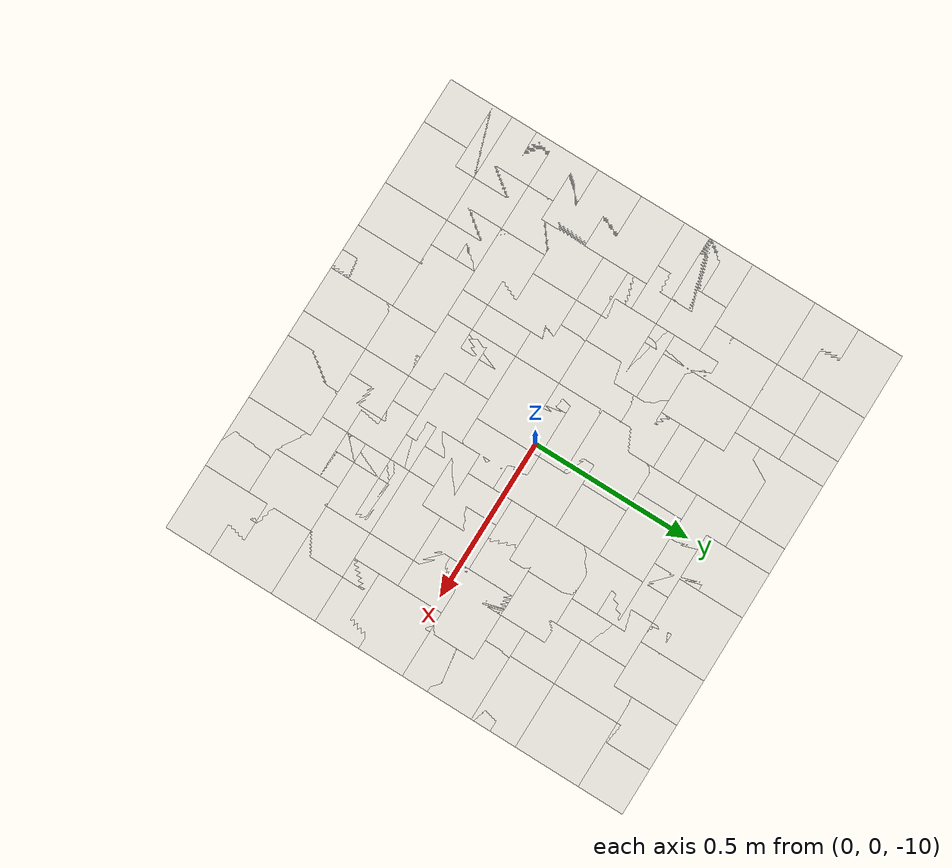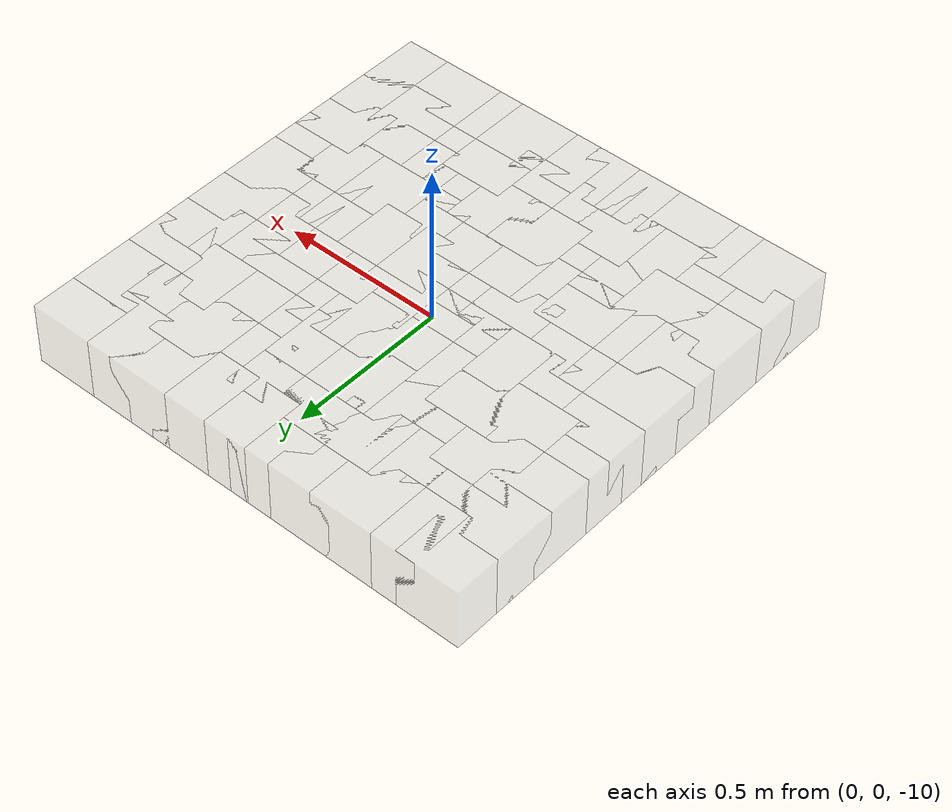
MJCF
<mujoco model="saber_targets">
  <compiler angle="radian"/>
  <option timestep="0.002"/>
  <asset>
    <material name="target_pool_cube" rgba="0.60 0.60 0.60 1.0" emission="0.55" specular="0.9" shininess="0.85"/>
    <material name="target_pool_face_left" rgba="0.05 0.25 1.0 1.0" emission="0.6" specular="0.9" shininess="0.9"/>
    <material name="target_pool_face_right" rgba="1.0 0.10 0.10 1.0" emission="0.6" specular="0.9" shininess="0.9"/>
  </asset>
  <worldbody>
    <body name="saber_targets_anchor" pos="0 0 0"/>
    <body name="saber_target_0" pos="-0.63 -0.63 -10.0" mocap="true">
      <geom name="saber_target_geom_0" type="box" size="0.1 0.1 0.1" rgba="0.5 0.5 0.5 0.2" mass="0.02" contype="2" conaffinity="1" condim="4" margin="0.0" gap="1.0" material="target_pool_cube"/>
      <geom name="saber_target_geom_0_marker_front" type="box" pos="0 0.112 0" size="0.07 0.008 0.07" rgba="0 0 0 0" contype="0" conaffinity="0" material="target_pool_face_left"/>
      <geom name="saber_target_geom_0_marker_top" type="box" pos="0 0 0.112" size="0.07 0.07 0.008" rgba="0 0 0 0" contype="0" conaffinity="0" material="target_pool_face_left"/>
      <geom name="saber_target_geom_0_marker_bottom" type="box" pos="0 0 -0.112" size="0.07 0.07 0.008" rgba="0 0 0 0" contype="0" conaffinity="0" material="target_pool_face_left"/>
      <geom name="saber_target_geom_0_marker_right" type="box" pos="0.112 0 0" size="0.008 0.07 0.07" rgba="0 0 0 0" contype="0" conaffinity="0" material="target_pool_face_left"/>
      <geom name="saber_target_geom_0_marker_left" type="box" pos="-0.112 0 0" size="0.008 0.07 0.07" rgba="0 0 0 0" contype="0" conaffinity="0" material="target_pool_face_left"/>
      <site name="saber_target_0_site" pos="0 0 0" size="0.01 0 0" rgba="1 1 1 0"/>
    </body>
    <body name="saber_target_1" pos="-0.49 -0.63 -10.0" mocap="true">
      <geom name="saber_target_geom_1" type="box" size="0.1 0.1 0.1" rgba="0.5 0.5 0.5 0.2" mass="0.02" contype="2" conaffinity="1" condim="4" margin="0.0" gap="1.0" material="target_pool_cube"/>
      <geom name="saber_target_geom_1_marker_front" type="box" pos="0 0.112 0" size="0.07 0.008 0.07" rgba="0 0 0 0" contype="0" conaffinity="0" material="target_pool_face_left"/>
      <geom name="saber_target_geom_1_marker_top" type="box" pos="0 0 0.112" size="0.07 0.07 0.008" rgba="0 0 0 0" contype="0" conaffinity="0" material="target_pool_face_left"/>
      <geom name="saber_target_geom_1_marker_bottom" type="box" pos="0 0 -0.112" size="0.07 0.07 0.008" rgba="0 0 0 0" contype="0" conaffinity="0" material="target_pool_face_left"/>
      <geom name="saber_target_geom_1_marker_right" type="box" pos="0.112 0 0" size="0.008 0.07 0.07" rgba="0 0 0 0" contype="0" conaffinity="0" material="target_pool_face_left"/>
      <geom name="saber_target_geom_1_marker_left" type="box" pos="-0.112 0 0" size="0.008 0.07 0.07" rgba="0 0 0 0" contype="0" conaffinity="0" material="target_pool_face_left"/>
      <site name="saber_target_1_site" pos="0 0 0" size="0.01 0 0" rgba="1 1 1 0"/>
    </body>
    <body name="saber_target_2" pos="-0.35 -0.63 -10.0" mocap="true">
      <geom name="saber_target_geom_2" type="box" size="0.1 0.1 0.1" rgba="0.5 0.5 0.5 0.2" mass="0.02" contype="2" conaffinity="1" condim="4" margin="0.0" gap="1.0" material="target_pool_cube"/>
      <geom name="saber_target_geom_2_marker_front" type="box" pos="0 0.112 0" size="0.07 0.008 0.07" rgba="0 0 0 0" contype="0" conaffinity="0" material="target_pool_face_left"/>
      <geom name="saber_target_geom_2_marker_top" type="box" pos="0 0 0.112" size="0.07 0.07 0.008" rgba="0 0 0 0" contype="0" conaffinity="0" material="target_pool_face_left"/>
      <geom name="saber_target_geom_2_marker_bottom" type="box" pos="0 0 -0.112" size="0.07 0.07 0.008" rgba="0 0 0 0" contype="0" conaffinity="0" material="target_pool_face_left"/>
      <geom name="saber_target_geom_2_marker_right" type="box" pos="0.112 0 0" size="0.008 0.07 0.07" rgba="0 0 0 0" contype="0" conaffinity="0" material="target_pool_face_left"/>
      <geom name="saber_target_geom_2_marker_left" type="box" pos="-0.112 0 0" size="0.008 0.07 0.07" rgba="0 0 0 0" contype="0" conaffinity="0" material="target_pool_face_left"/>
      <site name="saber_target_2_site" pos="0 0 0" size="0.01 0 0" rgba="1 1 1 0"/>
    </body>
    <body name="saber_target_3" pos="-0.20999999999999996 -0.63 -10.0" mocap="true">
      <geom name="saber_target_geom_3" type="box" size="0.1 0.1 0.1" rgba="0.5 0.5 0.5 0.2" mass="0.02" contype="2" conaffinity="1" condim="4" margin="0.0" gap="1.0" material="target_pool_cube"/>
      <geom name="saber_target_geom_3_marker_front" type="box" pos="0 0.112 0" size="0.07 0.008 0.07" rgba="0 0 0 0" contype="0" conaffinity="0" material="target_pool_face_left"/>
      <geom name="saber_target_geom_3_marker_top" type="box" pos="0 0 0.112" size="0.07 0.07 0.008" rgba="0 0 0 0" contype="0" conaffinity="0" material="target_pool_face_left"/>
      <geom name="saber_target_geom_3_marker_bottom" type="box" pos="0 0 -0.112" size="0.07 0.07 0.008" rgba="0 0 0 0" contype="0" conaffinity="0" material="target_pool_face_left"/>
      <geom name="saber_target_geom_3_marker_right" type="box" pos="0.112 0 0" size="0.008 0.07 0.07" rgba="0 0 0 0" contype="0" conaffinity="0" material="target_pool_face_left"/>
      <geom name="saber_target_geom_3_marker_left" type="box" pos="-0.112 0 0" size="0.008 0.07 0.07" rgba="0 0 0 0" contype="0" conaffinity="0" material="target_pool_face_left"/>
      <site name="saber_target_3_site" pos="0 0 0" size="0.01 0 0" rgba="1 1 1 0"/>
    </body>
    <body name="saber_target_4" pos="-0.06999999999999995 -0.63 -10.0" mocap="true">
      <geom name="saber_target_geom_4" type="box" size="0.1 0.1 0.1" rgba="0.5 0.5 0.5 0.2" mass="0.02" contype="2" conaffinity="1" condim="4" margin="0.0" gap="1.0" material="target_pool_cube"/>
      <geom name="saber_target_geom_4_marker_front" type="box" pos="0 0.112 0" size="0.07 0.008 0.07" rgba="0 0 0 0" contype="0" conaffinity="0" material="target_pool_face_left"/>
      <geom name="saber_target_geom_4_marker_top" type="box" pos="0 0 0.112" size="0.07 0.07 0.008" rgba="0 0 0 0" contype="0" conaffinity="0" material="target_pool_face_left"/>
      <geom name="saber_target_geom_4_marker_bottom" type="box" pos="0 0 -0.112" size="0.07 0.07 0.008" rgba="0 0 0 0" contype="0" conaffinity="0" material="target_pool_face_left"/>
      <geom name="saber_target_geom_4_marker_right" type="box" pos="0.112 0 0" size="0.008 0.07 0.07" rgba="0 0 0 0" contype="0" conaffinity="0" material="target_pool_face_left"/>
      <geom name="saber_target_geom_4_marker_left" type="box" pos="-0.112 0 0" size="0.008 0.07 0.07" rgba="0 0 0 0" contype="0" conaffinity="0" material="target_pool_face_left"/>
      <site name="saber_target_4_site" pos="0 0 0" size="0.01 0 0" rgba="1 1 1 0"/>
    </body>
    <body name="saber_target_5" pos="0.07000000000000006 -0.63 -10.0" mocap="true">
      <geom name="saber_target_geom_5" type="box" size="0.1 0.1 0.1" rgba="0.5 0.5 0.5 0.2" mass="0.02" contype="2" conaffinity="1" condim="4" margin="0.0" gap="1.0" material="target_pool_cube"/>
      <geom name="saber_target_geom_5_marker_front" type="box" pos="0 0.112 0" size="0.07 0.008 0.07" rgba="0 0 0 0" contype="0" conaffinity="0" material="target_pool_face_left"/>
      <geom name="saber_target_geom_5_marker_top" type="box" pos="0 0 0.112" size="0.07 0.07 0.008" rgba="0 0 0 0" contype="0" conaffinity="0" material="target_pool_face_left"/>
      <geom name="saber_target_geom_5_marker_bottom" type="box" pos="0 0 -0.112" size="0.07 0.07 0.008" rgba="0 0 0 0" contype="0" conaffinity="0" material="target_pool_face_left"/>
      <geom name="saber_target_geom_5_marker_right" type="box" pos="0.112 0 0" size="0.008 0.07 0.07" rgba="0 0 0 0" contype="0" conaffinity="0" material="target_pool_face_left"/>
      <geom name="saber_target_geom_5_marker_left" type="box" pos="-0.112 0 0" size="0.008 0.07 0.07" rgba="0 0 0 0" contype="0" conaffinity="0" material="target_pool_face_left"/>
      <site name="saber_target_5_site" pos="0 0 0" size="0.01 0 0" rgba="1 1 1 0"/>
    </body>
    <body name="saber_target_6" pos="0.21000000000000008 -0.63 -10.0" mocap="true">
      <geom name="saber_target_geom_6" type="box" size="0.1 0.1 0.1" rgba="0.5 0.5 0.5 0.2" mass="0.02" contype="2" conaffinity="1" condim="4" margin="0.0" gap="1.0" material="target_pool_cube"/>
      <geom name="saber_target_geom_6_marker_front" type="box" pos="0 0.112 0" size="0.07 0.008 0.07" rgba="0 0 0 0" contype="0" conaffinity="0" material="target_pool_face_left"/>
      <geom name="saber_target_geom_6_marker_top" type="box" pos="0 0 0.112" size="0.07 0.07 0.008" rgba="0 0 0 0" contype="0" conaffinity="0" material="target_pool_face_left"/>
      <geom name="saber_target_geom_6_marker_bottom" type="box" pos="0 0 -0.112" size="0.07 0.07 0.008" rgba="0 0 0 0" contype="0" conaffinity="0" material="target_pool_face_left"/>
      <geom name="saber_target_geom_6_marker_right" type="box" pos="0.112 0 0" size="0.008 0.07 0.07" rgba="0 0 0 0" contype="0" conaffinity="0" material="target_pool_face_left"/>
      <geom name="saber_target_geom_6_marker_left" type="box" pos="-0.112 0 0" size="0.008 0.07 0.07" rgba="0 0 0 0" contype="0" conaffinity="0" material="target_pool_face_left"/>
      <site name="saber_target_6_site" pos="0 0 0" size="0.01 0 0" rgba="1 1 1 0"/>
    </body>
    <body name="saber_target_7" pos="0.3500000000000001 -0.63 -10.0" mocap="true">
      <geom name="saber_target_geom_7" type="box" size="0.1 0.1 0.1" rgba="0.5 0.5 0.5 0.2" mass="0.02" contype="2" conaffinity="1" condim="4" margin="0.0" gap="1.0" material="target_pool_cube"/>
      <geom name="saber_target_geom_7_marker_front" type="box" pos="0 0.112 0" size="0.07 0.008 0.07" rgba="0 0 0 0" contype="0" conaffinity="0" material="target_pool_face_left"/>
      <geom name="saber_target_geom_7_marker_top" type="box" pos="0 0 0.112" size="0.07 0.07 0.008" rgba="0 0 0 0" contype="0" conaffinity="0" material="target_pool_face_left"/>
      <geom name="saber_target_geom_7_marker_bottom" type="box" pos="0 0 -0.112" size="0.07 0.07 0.008" rgba="0 0 0 0" contype="0" conaffinity="0" material="target_pool_face_left"/>
      <geom name="saber_target_geom_7_marker_right" type="box" pos="0.112 0 0" size="0.008 0.07 0.07" rgba="0 0 0 0" contype="0" conaffinity="0" material="target_pool_face_left"/>
      <geom name="saber_target_geom_7_marker_left" type="box" pos="-0.112 0 0" size="0.008 0.07 0.07" rgba="0 0 0 0" contype="0" conaffinity="0" material="target_pool_face_left"/>
      <site name="saber_target_7_site" pos="0 0 0" size="0.01 0 0" rgba="1 1 1 0"/>
    </body>
    <body name="saber_target_8" pos="0.4900000000000001 -0.63 -10.0" mocap="true">
      <geom name="saber_target_geom_8" type="box" size="0.1 0.1 0.1" rgba="0.5 0.5 0.5 0.2" mass="0.02" contype="2" conaffinity="1" condim="4" margin="0.0" gap="1.0" material="target_pool_cube"/>
      <geom name="saber_target_geom_8_marker_front" type="box" pos="0 0.112 0" size="0.07 0.008 0.07" rgba="0 0 0 0" contype="0" conaffinity="0" material="target_pool_face_left"/>
      <geom name="saber_target_geom_8_marker_top" type="box" pos="0 0 0.112" size="0.07 0.07 0.008" rgba="0 0 0 0" contype="0" conaffinity="0" material="target_pool_face_left"/>
      <geom name="saber_target_geom_8_marker_bottom" type="box" pos="0 0 -0.112" size="0.07 0.07 0.008" rgba="0 0 0 0" contype="0" conaffinity="0" material="target_pool_face_left"/>
      <geom name="saber_target_geom_8_marker_right" type="box" pos="0.112 0 0" size="0.008 0.07 0.07" rgba="0 0 0 0" contype="0" conaffinity="0" material="target_pool_face_left"/>
      <geom name="saber_target_geom_8_marker_left" type="box" pos="-0.112 0 0" size="0.008 0.07 0.07" rgba="0 0 0 0" contype="0" conaffinity="0" material="target_pool_face_left"/>
      <site name="saber_target_8_site" pos="0 0 0" size="0.01 0 0" rgba="1 1 1 0"/>
    </body>
    <body name="saber_target_9" pos="0.6300000000000002 -0.63 -10.0" mocap="true">
      <geom name="saber_target_geom_9" type="box" size="0.1 0.1 0.1" rgba="0.5 0.5 0.5 0.2" mass="0.02" contype="2" conaffinity="1" condim="4" margin="0.0" gap="1.0" material="target_pool_cube"/>
      <geom name="saber_target_geom_9_marker_front" type="box" pos="0 0.112 0" size="0.07 0.008 0.07" rgba="0 0 0 0" contype="0" conaffinity="0" material="target_pool_face_left"/>
      <geom name="saber_target_geom_9_marker_top" type="box" pos="0 0 0.112" size="0.07 0.07 0.008" rgba="0 0 0 0" contype="0" conaffinity="0" material="target_pool_face_left"/>
      <geom name="saber_target_geom_9_marker_bottom" type="box" pos="0 0 -0.112" size="0.07 0.07 0.008" rgba="0 0 0 0" contype="0" conaffinity="0" material="target_pool_face_left"/>
      <geom name="saber_target_geom_9_marker_right" type="box" pos="0.112 0 0" size="0.008 0.07 0.07" rgba="0 0 0 0" contype="0" conaffinity="0" material="target_pool_face_left"/>
      <geom name="saber_target_geom_9_marker_left" type="box" pos="-0.112 0 0" size="0.008 0.07 0.07" rgba="0 0 0 0" contype="0" conaffinity="0" material="target_pool_face_left"/>
      <site name="saber_target_9_site" pos="0 0 0" size="0.01 0 0" rgba="1 1 1 0"/>
    </body>
    <body name="saber_target_10" pos="-0.63 -0.49 -10.0" mocap="true">
      <geom name="saber_target_geom_10" type="box" size="0.1 0.1 0.1" rgba="0.5 0.5 0.5 0.2" mass="0.02" contype="2" conaffinity="1" condim="4" margin="0.0" gap="1.0" material="target_pool_cube"/>
      <geom name="saber_target_geom_10_marker_front" type="box" pos="0 0.112 0" size="0.07 0.008 0.07" rgba="0 0 0 0" contype="0" conaffinity="0" material="target_pool_face_left"/>
      <geom name="saber_target_geom_10_marker_top" type="box" pos="0 0 0.112" size="0.07 0.07 0.008" rgba="0 0 0 0" contype="0" conaffinity="0" material="target_pool_face_left"/>
      <geom name="saber_target_geom_10_marker_bottom" type="box" pos="0 0 -0.112" size="0.07 0.07 0.008" rgba="0 0 0 0" contype="0" conaffinity="0" material="target_pool_face_left"/>
      <geom name="saber_target_geom_10_marker_right" type="box" pos="0.112 0 0" size="0.008 0.07 0.07" rgba="0 0 0 0" contype="0" conaffinity="0" material="target_pool_face_left"/>
      <geom name="saber_target_geom_10_marker_left" type="box" pos="-0.112 0 0" size="0.008 0.07 0.07" rgba="0 0 0 0" contype="0" conaffinity="0" material="target_pool_face_left"/>
      <site name="saber_target_10_site" pos="0 0 0" size="0.01 0 0" rgba="1 1 1 0"/>
    </body>
    <body name="saber_target_11" pos="-0.49 -0.49 -10.0" mocap="true">
      <geom name="saber_target_geom_11" type="box" size="0.1 0.1 0.1" rgba="0.5 0.5 0.5 0.2" mass="0.02" contype="2" conaffinity="1" condim="4" margin="0.0" gap="1.0" material="target_pool_cube"/>
      <geom name="saber_target_geom_11_marker_front" type="box" pos="0 0.112 0" size="0.07 0.008 0.07" rgba="0 0 0 0" contype="0" conaffinity="0" material="target_pool_face_left"/>
      <geom name="saber_target_geom_11_marker_top" type="box" pos="0 0 0.112" size="0.07 0.07 0.008" rgba="0 0 0 0" contype="0" conaffinity="0" material="target_pool_face_left"/>
      <geom name="saber_target_geom_11_marker_bottom" type="box" pos="0 0 -0.112" size="0.07 0.07 0.008" rgba="0 0 0 0" contype="0" conaffinity="0" material="target_pool_face_left"/>
      <geom name="saber_target_geom_11_marker_right" type="box" pos="0.112 0 0" size="0.008 0.07 0.07" rgba="0 0 0 0" contype="0" conaffinity="0" material="target_pool_face_left"/>
      <geom name="saber_target_geom_11_marker_left" type="box" pos="-0.112 0 0" size="0.008 0.07 0.07" rgba="0 0 0 0" contype="0" conaffinity="0" material="target_pool_face_left"/>
      <site name="saber_target_11_site" pos="0 0 0" size="0.01 0 0" rgba="1 1 1 0"/>
    </body>
    <body name="saber_target_12" pos="-0.35 -0.49 -10.0" mocap="true">
      <geom name="saber_target_geom_12" type="box" size="0.1 0.1 0.1" rgba="0.5 0.5 0.5 0.2" mass="0.02" contype="2" conaffinity="1" condim="4" margin="0.0" gap="1.0" material="target_pool_cube"/>
      <geom name="saber_target_geom_12_marker_front" type="box" pos="0 0.112 0" size="0.07 0.008 0.07" rgba="0 0 0 0" contype="0" conaffinity="0" material="target_pool_face_left"/>
      <geom name="saber_target_geom_12_marker_top" type="box" pos="0 0 0.112" size="0.07 0.07 0.008" rgba="0 0 0 0" contype="0" conaffinity="0" material="target_pool_face_left"/>
      <geom name="saber_target_geom_12_marker_bottom" type="box" pos="0 0 -0.112" size="0.07 0.07 0.008" rgba="0 0 0 0" contype="0" conaffinity="0" material="target_pool_face_left"/>
      <geom name="saber_target_geom_12_marker_right" type="box" pos="0.112 0 0" size="0.008 0.07 0.07" rgba="0 0 0 0" contype="0" conaffinity="0" material="target_pool_face_left"/>
      <geom name="saber_target_geom_12_marker_left" type="box" pos="-0.112 0 0" size="0.008 0.07 0.07" rgba="0 0 0 0" contype="0" conaffinity="0" material="target_pool_face_left"/>
      <site name="saber_target_12_site" pos="0 0 0" size="0.01 0 0" rgba="1 1 1 0"/>
    </body>
    <body name="saber_target_13" pos="-0.20999999999999996 -0.49 -10.0" mocap="true">
      <geom name="saber_target_geom_13" type="box" size="0.1 0.1 0.1" rgba="0.5 0.5 0.5 0.2" mass="0.02" contype="2" conaffinity="1" condim="4" margin="0.0" gap="1.0" material="target_pool_cube"/>
      <geom name="saber_target_geom_13_marker_front" type="box" pos="0 0.112 0" size="0.07 0.008 0.07" rgba="0 0 0 0" contype="0" conaffinity="0" material="target_pool_face_left"/>
      <geom name="saber_target_geom_13_marker_top" type="box" pos="0 0 0.112" size="0.07 0.07 0.008" rgba="0 0 0 0" contype="0" conaffinity="0" material="target_pool_face_left"/>
      <geom name="saber_target_geom_13_marker_bottom" type="box" pos="0 0 -0.112" size="0.07 0.07 0.008" rgba="0 0 0 0" contype="0" conaffinity="0" material="target_pool_face_left"/>
      <geom name="saber_target_geom_13_marker_right" type="box" pos="0.112 0 0" size="0.008 0.07 0.07" rgba="0 0 0 0" contype="0" conaffinity="0" material="target_pool_face_left"/>
      <geom name="saber_target_geom_13_marker_left" type="box" pos="-0.112 0 0" size="0.008 0.07 0.07" rgba="0 0 0 0" contype="0" conaffinity="0" material="target_pool_face_left"/>
      <site name="saber_target_13_site" pos="0 0 0" size="0.01 0 0" rgba="1 1 1 0"/>
    </body>
    <body name="saber_target_14" pos="-0.06999999999999995 -0.49 -10.0" mocap="true">
      <geom name="saber_target_geom_14" type="box" size="0.1 0.1 0.1" rgba="0.5 0.5 0.5 0.2" mass="0.02" contype="2" conaffinity="1" condim="4" margin="0.0" gap="1.0" material="target_pool_cube"/>
      <geom name="saber_target_geom_14_marker_front" type="box" pos="0 0.112 0" size="0.07 0.008 0.07" rgba="0 0 0 0" contype="0" conaffinity="0" material="target_pool_face_left"/>
      <geom name="saber_target_geom_14_marker_top" type="box" pos="0 0 0.112" size="0.07 0.07 0.008" rgba="0 0 0 0" contype="0" conaffinity="0" material="target_pool_face_left"/>
      <geom name="saber_target_geom_14_marker_bottom" type="box" pos="0 0 -0.112" size="0.07 0.07 0.008" rgba="0 0 0 0" contype="0" conaffinity="0" material="target_pool_face_left"/>
      <geom name="saber_target_geom_14_marker_right" type="box" pos="0.112 0 0" size="0.008 0.07 0.07" rgba="0 0 0 0" contype="0" conaffinity="0" material="target_pool_face_left"/>
      <geom name="saber_target_geom_14_marker_left" type="box" pos="-0.112 0 0" size="0.008 0.07 0.07" rgba="0 0 0 0" contype="0" conaffinity="0" material="target_pool_face_left"/>
      <site name="saber_target_14_site" pos="0 0 0" size="0.01 0 0" rgba="1 1 1 0"/>
    </body>
    <body name="saber_target_15" pos="0.07000000000000006 -0.49 -10.0" mocap="true">
      <geom name="saber_target_geom_15" type="box" size="0.1 0.1 0.1" rgba="0.5 0.5 0.5 0.2" mass="0.02" contype="2" conaffinity="1" condim="4" margin="0.0" gap="1.0" material="target_pool_cube"/>
      <geom name="saber_target_geom_15_marker_front" type="box" pos="0 0.112 0" size="0.07 0.008 0.07" rgba="0 0 0 0" contype="0" conaffinity="0" material="target_pool_face_left"/>
      <geom name="saber_target_geom_15_marker_top" type="box" pos="0 0 0.112" size="0.07 0.07 0.008" rgba="0 0 0 0" contype="0" conaffinity="0" material="target_pool_face_left"/>
      <geom name="saber_target_geom_15_marker_bottom" type="box" pos="0 0 -0.112" size="0.07 0.07 0.008" rgba="0 0 0 0" contype="0" conaffinity="0" material="target_pool_face_left"/>
      <geom name="saber_target_geom_15_marker_right" type="box" pos="0.112 0 0" size="0.008 0.07 0.07" rgba="0 0 0 0" contype="0" conaffinity="0" material="target_pool_face_left"/>
      <geom name="saber_target_geom_15_marker_left" type="box" pos="-0.112 0 0" size="0.008 0.07 0.07" rgba="0 0 0 0" contype="0" conaffinity="0" material="target_pool_face_left"/>
      <site name="saber_target_15_site" pos="0 0 0" size="0.01 0 0" rgba="1 1 1 0"/>
    </body>
    <body name="saber_target_16" pos="0.21000000000000008 -0.49 -10.0" mocap="true">
      <geom name="saber_target_geom_16" type="box" size="0.1 0.1 0.1" rgba="0.5 0.5 0.5 0.2" mass="0.02" contype="2" conaffinity="1" condim="4" margin="0.0" gap="1.0" material="target_pool_cube"/>
      <geom name="saber_target_geom_16_marker_front" type="box" pos="0 0.112 0" size="0.07 0.008 0.07" rgba="0 0 0 0" contype="0" conaffinity="0" material="target_pool_face_left"/>
      <geom name="saber_target_geom_16_marker_top" type="box" pos="0 0 0.112" size="0.07 0.07 0.008" rgba="0 0 0 0" contype="0" conaffinity="0" material="target_pool_face_left"/>
      <geom name="saber_target_geom_16_marker_bottom" type="box" pos="0 0 -0.112" size="0.07 0.07 0.008" rgba="0 0 0 0" contype="0" conaffinity="0" material="target_pool_face_left"/>
      <geom name="saber_target_geom_16_marker_right" type="box" pos="0.112 0 0" size="0.008 0.07 0.07" rgba="0 0 0 0" contype="0" conaffinity="0" material="target_pool_face_left"/>
      <geom name="saber_target_geom_16_marker_left" type="box" pos="-0.112 0 0" size="0.008 0.07 0.07" rgba="0 0 0 0" contype="0" conaffinity="0" material="target_pool_face_left"/>
      <site name="saber_target_16_site" pos="0 0 0" size="0.01 0 0" rgba="1 1 1 0"/>
    </body>
    <body name="saber_target_17" pos="0.3500000000000001 -0.49 -10.0" mocap="true">
      <geom name="saber_target_geom_17" type="box" size="0.1 0.1 0.1" rgba="0.5 0.5 0.5 0.2" mass="0.02" contype="2" conaffinity="1" condim="4" margin="0.0" gap="1.0" material="target_pool_cube"/>
      <geom name="saber_target_geom_17_marker_front" type="box" pos="0 0.112 0" size="0.07 0.008 0.07" rgba="0 0 0 0" contype="0" conaffinity="0" material="target_pool_face_left"/>
      <geom name="saber_target_geom_17_marker_top" type="box" pos="0 0 0.112" size="0.07 0.07 0.008" rgba="0 0 0 0" contype="0" conaffinity="0" material="target_pool_face_left"/>
      <geom name="saber_target_geom_17_marker_bottom" type="box" pos="0 0 -0.112" size="0.07 0.07 0.008" rgba="0 0 0 0" contype="0" conaffinity="0" material="target_pool_face_left"/>
      <geom name="saber_target_geom_17_marker_right" type="box" pos="0.112 0 0" size="0.008 0.07 0.07" rgba="0 0 0 0" contype="0" conaffinity="0" material="target_pool_face_left"/>
      <geom name="saber_target_geom_17_marker_left" type="box" pos="-0.112 0 0" size="0.008 0.07 0.07" rgba="0 0 0 0" contype="0" conaffinity="0" material="target_pool_face_left"/>
      <site name="saber_target_17_site" pos="0 0 0" size="0.01 0 0" rgba="1 1 1 0"/>
    </body>
    <body name="saber_target_18" pos="0.4900000000000001 -0.49 -10.0" mocap="true">
      <geom name="saber_target_geom_18" type="box" size="0.1 0.1 0.1" rgba="0.5 0.5 0.5 0.2" mass="0.02" contype="2" conaffinity="1" condim="4" margin="0.0" gap="1.0" material="target_pool_cube"/>
      <geom name="saber_target_geom_18_marker_front" type="box" pos="0 0.112 0" size="0.07 0.008 0.07" rgba="0 0 0 0" contype="0" conaffinity="0" material="target_pool_face_left"/>
      <geom name="saber_target_geom_18_marker_top" type="box" pos="0 0 0.112" size="0.07 0.07 0.008" rgba="0 0 0 0" contype="0" conaffinity="0" material="target_pool_face_left"/>
      <geom name="saber_target_geom_18_marker_bottom" type="box" pos="0 0 -0.112" size="0.07 0.07 0.008" rgba="0 0 0 0" contype="0" conaffinity="0" material="target_pool_face_left"/>
      <geom name="saber_target_geom_18_marker_right" type="box" pos="0.112 0 0" size="0.008 0.07 0.07" rgba="0 0 0 0" contype="0" conaffinity="0" material="target_pool_face_left"/>
      <geom name="saber_target_geom_18_marker_left" type="box" pos="-0.112 0 0" size="0.008 0.07 0.07" rgba="0 0 0 0" contype="0" conaffinity="0" material="target_pool_face_left"/>
      <site name="saber_target_18_site" pos="0 0 0" size="0.01 0 0" rgba="1 1 1 0"/>
    </body>
    <body name="saber_target_19" pos="0.6300000000000002 -0.49 -10.0" mocap="true">
      <geom name="saber_target_geom_19" type="box" size="0.1 0.1 0.1" rgba="0.5 0.5 0.5 0.2" mass="0.02" contype="2" conaffinity="1" condim="4" margin="0.0" gap="1.0" material="target_pool_cube"/>
      <geom name="saber_target_geom_19_marker_front" type="box" pos="0 0.112 0" size="0.07 0.008 0.07" rgba="0 0 0 0" contype="0" conaffinity="0" material="target_pool_face_left"/>
      <geom name="saber_target_geom_19_marker_top" type="box" pos="0 0 0.112" size="0.07 0.07 0.008" rgba="0 0 0 0" contype="0" conaffinity="0" material="target_pool_face_left"/>
      <geom name="saber_target_geom_19_marker_bottom" type="box" pos="0 0 -0.112" size="0.07 0.07 0.008" rgba="0 0 0 0" contype="0" conaffinity="0" material="target_pool_face_left"/>
      <geom name="saber_target_geom_19_marker_right" type="box" pos="0.112 0 0" size="0.008 0.07 0.07" rgba="0 0 0 0" contype="0" conaffinity="0" material="target_pool_face_left"/>
      <geom name="saber_target_geom_19_marker_left" type="box" pos="-0.112 0 0" size="0.008 0.07 0.07" rgba="0 0 0 0" contype="0" conaffinity="0" material="target_pool_face_left"/>
      <site name="saber_target_19_site" pos="0 0 0" size="0.01 0 0" rgba="1 1 1 0"/>
    </body>
    <body name="saber_target_20" pos="-0.63 -0.35 -10.0" mocap="true">
      <geom name="saber_target_geom_20" type="box" size="0.1 0.1 0.1" rgba="0.5 0.5 0.5 0.2" mass="0.02" contype="2" conaffinity="1" condim="4" margin="0.0" gap="1.0" material="target_pool_cube"/>
      <geom name="saber_target_geom_20_marker_front" type="box" pos="0 0.112 0" size="0.07 0.008 0.07" rgba="0 0 0 0" contype="0" conaffinity="0" material="target_pool_face_left"/>
      <geom name="saber_target_geom_20_marker_top" type="box" pos="0 0 0.112" size="0.07 0.07 0.008" rgba="0 0 0 0" contype="0" conaffinity="0" material="target_pool_face_left"/>
      <geom name="saber_target_geom_20_marker_bottom" type="box" pos="0 0 -0.112" size="0.07 0.07 0.008" rgba="0 0 0 0" contype="0" conaffinity="0" material="target_pool_face_left"/>
      <geom name="saber_target_geom_20_marker_right" type="box" pos="0.112 0 0" size="0.008 0.07 0.07" rgba="0 0 0 0" contype="0" conaffinity="0" material="target_pool_face_left"/>
      <geom name="saber_target_geom_20_marker_left" type="box" pos="-0.112 0 0" size="0.008 0.07 0.07" rgba="0 0 0 0" contype="0" conaffinity="0" material="target_pool_face_left"/>
      <site name="saber_target_20_site" pos="0 0 0" size="0.01 0 0" rgba="1 1 1 0"/>
    </body>
    <body name="saber_target_21" pos="-0.49 -0.35 -10.0" mocap="true">
      <geom name="saber_target_geom_21" type="box" size="0.1 0.1 0.1" rgba="0.5 0.5 0.5 0.2" mass="0.02" contype="2" conaffinity="1" condim="4" margin="0.0" gap="1.0" material="target_pool_cube"/>
      <geom name="saber_target_geom_21_marker_front" type="box" pos="0 0.112 0" size="0.07 0.008 0.07" rgba="0 0 0 0" contype="0" conaffinity="0" material="target_pool_face_left"/>
      <geom name="saber_target_geom_21_marker_top" type="box" pos="0 0 0.112" size="0.07 0.07 0.008" rgba="0 0 0 0" contype="0" conaffinity="0" material="target_pool_face_left"/>
      <geom name="saber_target_geom_21_marker_bottom" type="box" pos="0 0 -0.112" size="0.07 0.07 0.008" rgba="0 0 0 0" contype="0" conaffinity="0" material="target_pool_face_left"/>
      <geom name="saber_target_geom_21_marker_right" type="box" pos="0.112 0 0" size="0.008 0.07 0.07" rgba="0 0 0 0" contype="0" conaffinity="0" material="target_pool_face_left"/>
      <geom name="saber_target_geom_21_marker_left" type="box" pos="-0.112 0 0" size="0.008 0.07 0.07" rgba="0 0 0 0" contype="0" conaffinity="0" material="target_pool_face_left"/>
      <site name="saber_target_21_site" pos="0 0 0" size="0.01 0 0" rgba="1 1 1 0"/>
    </body>
    <body name="saber_target_22" pos="-0.35 -0.35 -10.0" mocap="true">
      <geom name="saber_target_geom_22" type="box" size="0.1 0.1 0.1" rgba="0.5 0.5 0.5 0.2" mass="0.02" contype="2" conaffinity="1" condim="4" margin="0.0" gap="1.0" material="target_pool_cube"/>
      <geom name="saber_target_geom_22_marker_front" type="box" pos="0 0.112 0" size="0.07 0.008 0.07" rgba="0 0 0 0" contype="0" conaffinity="0" material="target_pool_face_left"/>
      <geom name="saber_target_geom_22_marker_top" type="box" pos="0 0 0.112" size="0.07 0.07 0.008" rgba="0 0 0 0" contype="0" conaffinity="0" material="target_pool_face_left"/>
      <geom name="saber_target_geom_22_marker_bottom" type="box" pos="0 0 -0.112" size="0.07 0.07 0.008" rgba="0 0 0 0" contype="0" conaffinity="0" material="target_pool_face_left"/>
      <geom name="saber_target_geom_22_marker_right" type="box" pos="0.112 0 0" size="0.008 0.07 0.07" rgba="0 0 0 0" contype="0" conaffinity="0" material="target_pool_face_left"/>
      <geom name="saber_target_geom_22_marker_left" type="box" pos="-0.112 0 0" size="0.008 0.07 0.07" rgba="0 0 0 0" contype="0" conaffinity="0" material="target_pool_face_left"/>
      <site name="saber_target_22_site" pos="0 0 0" size="0.01 0 0" rgba="1 1 1 0"/>
    </body>
    <body name="saber_target_23" pos="-0.20999999999999996 -0.35 -10.0" mocap="true">
      <geom name="saber_target_geom_23" type="box" size="0.1 0.1 0.1" rgba="0.5 0.5 0.5 0.2" mass="0.02" contype="2" conaffinity="1" condim="4" margin="0.0" gap="1.0" material="target_pool_cube"/>
      <geom name="saber_target_geom_23_marker_front" type="box" pos="0 0.112 0" size="0.07 0.008 0.07" rgba="0 0 0 0" contype="0" conaffinity="0" material="target_pool_face_left"/>
      <geom name="saber_target_geom_23_marker_top" type="box" pos="0 0 0.112" size="0.07 0.07 0.008" rgba="0 0 0 0" contype="0" conaffinity="0" material="target_pool_face_left"/>
      <geom name="saber_target_geom_23_marker_bottom" type="box" pos="0 0 -0.112" size="0.07 0.07 0.008" rgba="0 0 0 0" contype="0" conaffinity="0" material="target_pool_face_left"/>
      <geom name="saber_target_geom_23_marker_right" type="box" pos="0.112 0 0" size="0.008 0.07 0.07" rgba="0 0 0 0" contype="0" conaffinity="0" material="target_pool_face_left"/>
      <geom name="saber_target_geom_23_marker_left" type="box" pos="-0.112 0 0" size="0.008 0.07 0.07" rgba="0 0 0 0" contype="0" conaffinity="0" material="target_pool_face_left"/>
      <site name="saber_target_23_site" pos="0 0 0" size="0.01 0 0" rgba="1 1 1 0"/>
    </body>
    <body name="saber_target_24" pos="-0.06999999999999995 -0.35 -10.0" mocap="true">
      <geom name="saber_target_geom_24" type="box" size="0.1 0.1 0.1" rgba="0.5 0.5 0.5 0.2" mass="0.02" contype="2" conaffinity="1" condim="4" margin="0.0" gap="1.0" material="target_pool_cube"/>
      <geom name="saber_target_geom_24_marker_front" type="box" pos="0 0.112 0" size="0.07 0.008 0.07" rgba="0 0 0 0" contype="0" conaffinity="0" material="target_pool_face_left"/>
      <geom name="saber_target_geom_24_marker_top" type="box" pos="0 0 0.112" size="0.07 0.07 0.008" rgba="0 0 0 0" contype="0" conaffinity="0" material="target_pool_face_left"/>
      <geom name="saber_target_geom_24_marker_bottom" type="box" pos="0 0 -0.112" size="0.07 0.07 0.008" rgba="0 0 0 0" contype="0" conaffinity="0" material="target_pool_face_left"/>
      <geom name="saber_target_geom_24_marker_right" type="box" pos="0.112 0 0" size="0.008 0.07 0.07" rgba="0 0 0 0" contype="0" conaffinity="0" material="target_pool_face_left"/>
      <geom name="saber_target_geom_24_marker_left" type="box" pos="-0.112 0 0" size="0.008 0.07 0.07" rgba="0 0 0 0" contype="0" conaffinity="0" material="target_pool_face_left"/>
      <site name="saber_target_24_site" pos="0 0 0" size="0.01 0 0" rgba="1 1 1 0"/>
    </body>
    <body name="saber_target_25" pos="0.07000000000000006 -0.35 -10.0" mocap="true">
      <geom name="saber_target_geom_25" type="box" size="0.1 0.1 0.1" rgba="0.5 0.5 0.5 0.2" mass="0.02" contype="2" conaffinity="1" condim="4" margin="0.0" gap="1.0" material="target_pool_cube"/>
      <geom name="saber_target_geom_25_marker_front" type="box" pos="0 0.112 0" size="0.07 0.008 0.07" rgba="0 0 0 0" contype="0" conaffinity="0" material="target_pool_face_left"/>
      <geom name="saber_target_geom_25_marker_top" type="box" pos="0 0 0.112" size="0.07 0.07 0.008" rgba="0 0 0 0" contype="0" conaffinity="0" material="target_pool_face_left"/>
      <geom name="saber_target_geom_25_marker_bottom" type="box" pos="0 0 -0.112" size="0.07 0.07 0.008" rgba="0 0 0 0" contype="0" conaffinity="0" material="target_pool_face_left"/>
      <geom name="saber_target_geom_25_marker_right" type="box" pos="0.112 0 0" size="0.008 0.07 0.07" rgba="0 0 0 0" contype="0" conaffinity="0" material="target_pool_face_left"/>
      <geom name="saber_target_geom_25_marker_left" type="box" pos="-0.112 0 0" size="0.008 0.07 0.07" rgba="0 0 0 0" contype="0" conaffinity="0" material="target_pool_face_left"/>
      <site name="saber_target_25_site" pos="0 0 0" size="0.01 0 0" rgba="1 1 1 0"/>
    </body>
    <body name="saber_target_26" pos="0.21000000000000008 -0.35 -10.0" mocap="true">
      <geom name="saber_target_geom_26" type="box" size="0.1 0.1 0.1" rgba="0.5 0.5 0.5 0.2" mass="0.02" contype="2" conaffinity="1" condim="4" margin="0.0" gap="1.0" material="target_pool_cube"/>
      <geom name="saber_target_geom_26_marker_front" type="box" pos="0 0.112 0" size="0.07 0.008 0.07" rgba="0 0 0 0" contype="0" conaffinity="0" material="target_pool_face_left"/>
      <geom name="saber_target_geom_26_marker_top" type="box" pos="0 0 0.112" size="0.07 0.07 0.008" rgba="0 0 0 0" contype="0" conaffinity="0" material="target_pool_face_left"/>
      <geom name="saber_target_geom_26_marker_bottom" type="box" pos="0 0 -0.112" size="0.07 0.07 0.008" rgba="0 0 0 0" contype="0" conaffinity="0" material="target_pool_face_left"/>
      <geom name="saber_target_geom_26_marker_right" type="box" pos="0.112 0 0" size="0.008 0.07 0.07" rgba="0 0 0 0" contype="0" conaffinity="0" material="target_pool_face_left"/>
      <geom name="saber_target_geom_26_marker_left" type="box" pos="-0.112 0 0" size="0.008 0.07 0.07" rgba="0 0 0 0" contype="0" conaffinity="0" material="target_pool_face_left"/>
      <site name="saber_target_26_site" pos="0 0 0" size="0.01 0 0" rgba="1 1 1 0"/>
    </body>
    <body name="saber_target_27" pos="0.3500000000000001 -0.35 -10.0" mocap="true">
      <geom name="saber_target_geom_27" type="box" size="0.1 0.1 0.1" rgba="0.5 0.5 0.5 0.2" mass="0.02" contype="2" conaffinity="1" condim="4" margin="0.0" gap="1.0" material="target_pool_cube"/>
      <geom name="saber_target_geom_27_marker_front" type="box" pos="0 0.112 0" size="0.07 0.008 0.07" rgba="0 0 0 0" contype="0" conaffinity="0" material="target_pool_face_left"/>
      <geom name="saber_target_geom_27_marker_top" type="box" pos="0 0 0.112" size="0.07 0.07 0.008" rgba="0 0 0 0" contype="0" conaffinity="0" material="target_pool_face_left"/>
      <geom name="saber_target_geom_27_marker_bottom" type="box" pos="0 0 -0.112" size="0.07 0.07 0.008" rgba="0 0 0 0" contype="0" conaffinity="0" material="target_pool_face_left"/>
      <geom name="saber_target_geom_27_marker_right" type="box" pos="0.112 0 0" size="0.008 0.07 0.07" rgba="0 0 0 0" contype="0" conaffinity="0" material="target_pool_face_left"/>
      <geom name="saber_target_geom_27_marker_left" type="box" pos="-0.112 0 0" size="0.008 0.07 0.07" rgba="0 0 0 0" contype="0" conaffinity="0" material="target_pool_face_left"/>
      <site name="saber_target_27_site" pos="0 0 0" size="0.01 0 0" rgba="1 1 1 0"/>
    </body>
    <body name="saber_target_28" pos="0.4900000000000001 -0.35 -10.0" mocap="true">
      <geom name="saber_target_geom_28" type="box" size="0.1 0.1 0.1" rgba="0.5 0.5 0.5 0.2" mass="0.02" contype="2" conaffinity="1" condim="4" margin="0.0" gap="1.0" material="target_pool_cube"/>
      <geom name="saber_target_geom_28_marker_front" type="box" pos="0 0.112 0" size="0.07 0.008 0.07" rgba="0 0 0 0" contype="0" conaffinity="0" material="target_pool_face_left"/>
      <geom name="saber_target_geom_28_marker_top" type="box" pos="0 0 0.112" size="0.07 0.07 0.008" rgba="0 0 0 0" contype="0" conaffinity="0" material="target_pool_face_left"/>
      <geom name="saber_target_geom_28_marker_bottom" type="box" pos="0 0 -0.112" size="0.07 0.07 0.008" rgba="0 0 0 0" contype="0" conaffinity="0" material="target_pool_face_left"/>
      <geom name="saber_target_geom_28_marker_right" type="box" pos="0.112 0 0" size="0.008 0.07 0.07" rgba="0 0 0 0" contype="0" conaffinity="0" material="target_pool_face_left"/>
      <geom name="saber_target_geom_28_marker_left" type="box" pos="-0.112 0 0" size="0.008 0.07 0.07" rgba="0 0 0 0" contype="0" conaffinity="0" material="target_pool_face_left"/>
      <site name="saber_target_28_site" pos="0 0 0" size="0.01 0 0" rgba="1 1 1 0"/>
    </body>
    <body name="saber_target_29" pos="0.6300000000000002 -0.35 -10.0" mocap="true">
      <geom name="saber_target_geom_29" type="box" size="0.1 0.1 0.1" rgba="0.5 0.5 0.5 0.2" mass="0.02" contype="2" conaffinity="1" condim="4" margin="0.0" gap="1.0" material="target_pool_cube"/>
      <geom name="saber_target_geom_29_marker_front" type="box" pos="0 0.112 0" size="0.07 0.008 0.07" rgba="0 0 0 0" contype="0" conaffinity="0" material="target_pool_face_left"/>
      <geom name="saber_target_geom_29_marker_top" type="box" pos="0 0 0.112" size="0.07 0.07 0.008" rgba="0 0 0 0" contype="0" conaffinity="0" material="target_pool_face_left"/>
      <geom name="saber_target_geom_29_marker_bottom" type="box" pos="0 0 -0.112" size="0.07 0.07 0.008" rgba="0 0 0 0" contype="0" conaffinity="0" material="target_pool_face_left"/>
      <geom name="saber_target_geom_29_marker_right" type="box" pos="0.112 0 0" size="0.008 0.07 0.07" rgba="0 0 0 0" contype="0" conaffinity="0" material="target_pool_face_left"/>
      <geom name="saber_target_geom_29_marker_left" type="box" pos="-0.112 0 0" size="0.008 0.07 0.07" rgba="0 0 0 0" contype="0" conaffinity="0" material="target_pool_face_left"/>
      <site name="saber_target_29_site" pos="0 0 0" size="0.01 0 0" rgba="1 1 1 0"/>
    </body>
    <body name="saber_target_30" pos="-0.63 -0.20999999999999996 -10.0" mocap="true">
      <geom name="saber_target_geom_30" type="box" size="0.1 0.1 0.1" rgba="0.5 0.5 0.5 0.2" mass="0.02" contype="2" conaffinity="1" condim="4" margin="0.0" gap="1.0" material="target_pool_cube"/>
      <geom name="saber_target_geom_30_marker_front" type="box" pos="0 0.112 0" size="0.07 0.008 0.07" rgba="0 0 0 0" contype="0" conaffinity="0" material="target_pool_face_left"/>
      <geom name="saber_target_geom_30_marker_top" type="box" pos="0 0 0.112" size="0.07 0.07 0.008" rgba="0 0 0 0" contype="0" conaffinity="0" material="target_pool_face_left"/>
      <geom name="saber_target_geom_30_marker_bottom" type="box" pos="0 0 -0.112" size="0.07 0.07 0.008" rgba="0 0 0 0" contype="0" conaffinity="0" material="target_pool_face_left"/>
      <geom name="saber_target_geom_30_marker_right" type="box" pos="0.112 0 0" size="0.008 0.07 0.07" rgba="0 0 0 0" contype="0" conaffinity="0" material="target_pool_face_left"/>
      <geom name="saber_target_geom_30_marker_left" type="box" pos="-0.112 0 0" size="0.008 0.07 0.07" rgba="0 0 0 0" contype="0" conaffinity="0" material="target_pool_face_left"/>
      <site name="saber_target_30_site" pos="0 0 0" size="0.01 0 0" rgba="1 1 1 0"/>
    </body>
    <body name="saber_target_31" pos="-0.49 -0.20999999999999996 -10.0" mocap="true">
      <geom name="saber_target_geom_31" type="box" size="0.1 0.1 0.1" rgba="0.5 0.5 0.5 0.2" mass="0.02" contype="2" conaffinity="1" condim="4" margin="0.0" gap="1.0" material="target_pool_cube"/>
      <geom name="saber_target_geom_31_marker_front" type="box" pos="0 0.112 0" size="0.07 0.008 0.07" rgba="0 0 0 0" contype="0" conaffinity="0" material="target_pool_face_left"/>
      <geom name="saber_target_geom_31_marker_top" type="box" pos="0 0 0.112" size="0.07 0.07 0.008" rgba="0 0 0 0" contype="0" conaffinity="0" material="target_pool_face_left"/>
      <geom name="saber_target_geom_31_marker_bottom" type="box" pos="0 0 -0.112" size="0.07 0.07 0.008" rgba="0 0 0 0" contype="0" conaffinity="0" material="target_pool_face_left"/>
      <geom name="saber_target_geom_31_marker_right" type="box" pos="0.112 0 0" size="0.008 0.07 0.07" rgba="0 0 0 0" contype="0" conaffinity="0" material="target_pool_face_left"/>
      <geom name="saber_target_geom_31_marker_left" type="box" pos="-0.112 0 0" size="0.008 0.07 0.07" rgba="0 0 0 0" contype="0" conaffinity="0" material="target_pool_face_left"/>
      <site name="saber_target_31_site" pos="0 0 0" size="0.01 0 0" rgba="1 1 1 0"/>
    </body>
    <body name="saber_target_32" pos="-0.35 -0.20999999999999996 -10.0" mocap="true">
      <geom name="saber_target_geom_32" type="box" size="0.1 0.1 0.1" rgba="0.5 0.5 0.5 0.2" mass="0.02" contype="2" conaffinity="1" condim="4" margin="0.0" gap="1.0" material="target_pool_cube"/>
      <geom name="saber_target_geom_32_marker_front" type="box" pos="0 0.112 0" size="0.07 0.008 0.07" rgba="0 0 0 0" contype="0" conaffinity="0" material="target_pool_face_left"/>
      <geom name="saber_target_geom_32_marker_top" type="box" pos="0 0 0.112" size="0.07 0.07 0.008" rgba="0 0 0 0" contype="0" conaffinity="0" material="target_pool_face_left"/>
      <geom name="saber_target_geom_32_marker_bottom" type="box" pos="0 0 -0.112" size="0.07 0.07 0.008" rgba="0 0 0 0" contype="0" conaffinity="0" material="target_pool_face_left"/>
      <geom name="saber_target_geom_32_marker_right" type="box" pos="0.112 0 0" size="0.008 0.07 0.07" rgba="0 0 0 0" contype="0" conaffinity="0" material="target_pool_face_left"/>
      <geom name="saber_target_geom_32_marker_left" type="box" pos="-0.112 0 0" size="0.008 0.07 0.07" rgba="0 0 0 0" contype="0" conaffinity="0" material="target_pool_face_left"/>
      <site name="saber_target_32_site" pos="0 0 0" size="0.01 0 0" rgba="1 1 1 0"/>
    </body>
    <body name="saber_target_33" pos="-0.20999999999999996 -0.20999999999999996 -10.0" mocap="true">
      <geom name="saber_target_geom_33" type="box" size="0.1 0.1 0.1" rgba="0.5 0.5 0.5 0.2" mass="0.02" contype="2" conaffinity="1" condim="4" margin="0.0" gap="1.0" material="target_pool_cube"/>
      <geom name="saber_target_geom_33_marker_front" type="box" pos="0 0.112 0" size="0.07 0.008 0.07" rgba="0 0 0 0" contype="0" conaffinity="0" material="target_pool_face_left"/>
      <geom name="saber_target_geom_33_marker_top" type="box" pos="0 0 0.112" size="0.07 0.07 0.008" rgba="0 0 0 0" contype="0" conaffinity="0" material="target_pool_face_left"/>
      <geom name="saber_target_geom_33_marker_bottom" type="box" pos="0 0 -0.112" size="0.07 0.07 0.008" rgba="0 0 0 0" contype="0" conaffinity="0" material="target_pool_face_left"/>
      <geom name="saber_target_geom_33_marker_right" type="box" pos="0.112 0 0" size="0.008 0.07 0.07" rgba="0 0 0 0" contype="0" conaffinity="0" material="target_pool_face_left"/>
      <geom name="saber_target_geom_33_marker_left" type="box" pos="-0.112 0 0" size="0.008 0.07 0.07" rgba="0 0 0 0" contype="0" conaffinity="0" material="target_pool_face_left"/>
      <site name="saber_target_33_site" pos="0 0 0" size="0.01 0 0" rgba="1 1 1 0"/>
    </body>
    <body name="saber_target_34" pos="-0.06999999999999995 -0.20999999999999996 -10.0" mocap="true">
      <geom name="saber_target_geom_34" type="box" size="0.1 0.1 0.1" rgba="0.5 0.5 0.5 0.2" mass="0.02" contype="2" conaffinity="1" condim="4" margin="0.0" gap="1.0" material="target_pool_cube"/>
      <geom name="saber_target_geom_34_marker_front" type="box" pos="0 0.112 0" size="0.07 0.008 0.07" rgba="0 0 0 0" contype="0" conaffinity="0" material="target_pool_face_left"/>
      <geom name="saber_target_geom_34_marker_top" type="box" pos="0 0 0.112" size="0.07 0.07 0.008" rgba="0 0 0 0" contype="0" conaffinity="0" material="target_pool_face_left"/>
      <geom name="saber_target_geom_34_marker_bottom" type="box" pos="0 0 -0.112" size="0.07 0.07 0.008" rgba="0 0 0 0" contype="0" conaffinity="0" material="target_pool_face_left"/>
      <geom name="saber_target_geom_34_marker_right" type="box" pos="0.112 0 0" size="0.008 0.07 0.07" rgba="0 0 0 0" contype="0" conaffinity="0" material="target_pool_face_left"/>
      <geom name="saber_target_geom_34_marker_left" type="box" pos="-0.112 0 0" size="0.008 0.07 0.07" rgba="0 0 0 0" contype="0" conaffinity="0" material="target_pool_face_left"/>
      <site name="saber_target_34_site" pos="0 0 0" size="0.01 0 0" rgba="1 1 1 0"/>
    </body>
    <body name="saber_target_35" pos="0.07000000000000006 -0.20999999999999996 -10.0" mocap="true">
      <geom name="saber_target_geom_35" type="box" size="0.1 0.1 0.1" rgba="0.5 0.5 0.5 0.2" mass="0.02" contype="2" conaffinity="1" condim="4" margin="0.0" gap="1.0" material="target_pool_cube"/>
      <geom name="saber_target_geom_35_marker_front" type="box" pos="0 0.112 0" size="0.07 0.008 0.07" rgba="0 0 0 0" contype="0" conaffinity="0" material="target_pool_face_left"/>
      <geom name="saber_target_geom_35_marker_top" type="box" pos="0 0 0.112" size="0.07 0.07 0.008" rgba="0 0 0 0" contype="0" conaffinity="0" material="target_pool_face_left"/>
      <geom name="saber_target_geom_35_marker_bottom" type="box" pos="0 0 -0.112" size="0.07 0.07 0.008" rgba="0 0 0 0" contype="0" conaffinity="0" material="target_pool_face_left"/>
      <geom name="saber_target_geom_35_marker_right" type="box" pos="0.112 0 0" size="0.008 0.07 0.07" rgba="0 0 0 0" contype="0" conaffinity="0" material="target_pool_face_left"/>
      <geom name="saber_target_geom_35_marker_left" type="box" pos="-0.112 0 0" size="0.008 0.07 0.07" rgba="0 0 0 0" contype="0" conaffinity="0" material="target_pool_face_left"/>
      <site name="saber_target_35_site" pos="0 0 0" size="0.01 0 0" rgba="1 1 1 0"/>
    </body>
    <body name="saber_target_36" pos="0.21000000000000008 -0.20999999999999996 -10.0" mocap="true">
      <geom name="saber_target_geom_36" type="box" size="0.1 0.1 0.1" rgba="0.5 0.5 0.5 0.2" mass="0.02" contype="2" conaffinity="1" condim="4" margin="0.0" gap="1.0" material="target_pool_cube"/>
      <geom name="saber_target_geom_36_marker_front" type="box" pos="0 0.112 0" size="0.07 0.008 0.07" rgba="0 0 0 0" contype="0" conaffinity="0" material="target_pool_face_left"/>
      <geom name="saber_target_geom_36_marker_top" type="box" pos="0 0 0.112" size="0.07 0.07 0.008" rgba="0 0 0 0" contype="0" conaffinity="0" material="target_pool_face_left"/>
      <geom name="saber_target_geom_36_marker_bottom" type="box" pos="0 0 -0.112" size="0.07 0.07 0.008" rgba="0 0 0 0" contype="0" conaffinity="0" material="target_pool_face_left"/>
      <geom name="saber_target_geom_36_marker_right" type="box" pos="0.112 0 0" size="0.008 0.07 0.07" rgba="0 0 0 0" contype="0" conaffinity="0" material="target_pool_face_left"/>
      <geom name="saber_target_geom_36_marker_left" type="box" pos="-0.112 0 0" size="0.008 0.07 0.07" rgba="0 0 0 0" contype="0" conaffinity="0" material="target_pool_face_left"/>
      <site name="saber_target_36_site" pos="0 0 0" size="0.01 0 0" rgba="1 1 1 0"/>
    </body>
    <body name="saber_target_37" pos="0.3500000000000001 -0.20999999999999996 -10.0" mocap="true">
      <geom name="saber_target_geom_37" type="box" size="0.1 0.1 0.1" rgba="0.5 0.5 0.5 0.2" mass="0.02" contype="2" conaffinity="1" condim="4" margin="0.0" gap="1.0" material="target_pool_cube"/>
      <geom name="saber_target_geom_37_marker_front" type="box" pos="0 0.112 0" size="0.07 0.008 0.07" rgba="0 0 0 0" contype="0" conaffinity="0" material="target_pool_face_left"/>
      <geom name="saber_target_geom_37_marker_top" type="box" pos="0 0 0.112" size="0.07 0.07 0.008" rgba="0 0 0 0" contype="0" conaffinity="0" material="target_pool_face_left"/>
      <geom name="saber_target_geom_37_marker_bottom" type="box" pos="0 0 -0.112" size="0.07 0.07 0.008" rgba="0 0 0 0" contype="0" conaffinity="0" material="target_pool_face_left"/>
      <geom name="saber_target_geom_37_marker_right" type="box" pos="0.112 0 0" size="0.008 0.07 0.07" rgba="0 0 0 0" contype="0" conaffinity="0" material="target_pool_face_left"/>
      <geom name="saber_target_geom_37_marker_left" type="box" pos="-0.112 0 0" size="0.008 0.07 0.07" rgba="0 0 0 0" contype="0" conaffinity="0" material="target_pool_face_left"/>
      <site name="saber_target_37_site" pos="0 0 0" size="0.01 0 0" rgba="1 1 1 0"/>
    </body>
    <body name="saber_target_38" pos="0.4900000000000001 -0.20999999999999996 -10.0" mocap="true">
      <geom name="saber_target_geom_38" type="box" size="0.1 0.1 0.1" rgba="0.5 0.5 0.5 0.2" mass="0.02" contype="2" conaffinity="1" condim="4" margin="0.0" gap="1.0" material="target_pool_cube"/>
      <geom name="saber_target_geom_38_marker_front" type="box" pos="0 0.112 0" size="0.07 0.008 0.07" rgba="0 0 0 0" contype="0" conaffinity="0" material="target_pool_face_left"/>
      <geom name="saber_target_geom_38_marker_top" type="box" pos="0 0 0.112" size="0.07 0.07 0.008" rgba="0 0 0 0" contype="0" conaffinity="0" material="target_pool_face_left"/>
      <geom name="saber_target_geom_38_marker_bottom" type="box" pos="0 0 -0.112" size="0.07 0.07 0.008" rgba="0 0 0 0" contype="0" conaffinity="0" material="target_pool_face_left"/>
      <geom name="saber_target_geom_38_marker_right" type="box" pos="0.112 0 0" size="0.008 0.07 0.07" rgba="0 0 0 0" contype="0" conaffinity="0" material="target_pool_face_left"/>
      <geom name="saber_target_geom_38_marker_left" type="box" pos="-0.112 0 0" size="0.008 0.07 0.07" rgba="0 0 0 0" contype="0" conaffinity="0" material="target_pool_face_left"/>
      <site name="saber_target_38_site" pos="0 0 0" size="0.01 0 0" rgba="1 1 1 0"/>
    </body>
    <body name="saber_target_39" pos="0.6300000000000002 -0.20999999999999996 -10.0" mocap="true">
      <geom name="saber_target_geom_39" type="box" size="0.1 0.1 0.1" rgba="0.5 0.5 0.5 0.2" mass="0.02" contype="2" conaffinity="1" condim="4" margin="0.0" gap="1.0" material="target_pool_cube"/>
      <geom name="saber_target_geom_39_marker_front" type="box" pos="0 0.112 0" size="0.07 0.008 0.07" rgba="0 0 0 0" contype="0" conaffinity="0" material="target_pool_face_left"/>
      <geom name="saber_target_geom_39_marker_top" type="box" pos="0 0 0.112" size="0.07 0.07 0.008" rgba="0 0 0 0" contype="0" conaffinity="0" material="target_pool_face_left"/>
      <geom name="saber_target_geom_39_marker_bottom" type="box" pos="0 0 -0.112" size="0.07 0.07 0.008" rgba="0 0 0 0" contype="0" conaffinity="0" material="target_pool_face_left"/>
      <geom name="saber_target_geom_39_marker_right" type="box" pos="0.112 0 0" size="0.008 0.07 0.07" rgba="0 0 0 0" contype="0" conaffinity="0" material="target_pool_face_left"/>
      <geom name="saber_target_geom_39_marker_left" type="box" pos="-0.112 0 0" size="0.008 0.07 0.07" rgba="0 0 0 0" contype="0" conaffinity="0" material="target_pool_face_left"/>
      <site name="saber_target_39_site" pos="0 0 0" size="0.01 0 0" rgba="1 1 1 0"/>
    </body>
    <body name="saber_target_40" pos="-0.63 -0.06999999999999995 -10.0" mocap="true">
      <geom name="saber_target_geom_40" type="box" size="0.1 0.1 0.1" rgba="0.5 0.5 0.5 0.2" mass="0.02" contype="2" conaffinity="1" condim="4" margin="0.0" gap="1.0" material="target_pool_cube"/>
      <geom name="saber_target_geom_40_marker_front" type="box" pos="0 0.112 0" size="0.07 0.008 0.07" rgba="0 0 0 0" contype="0" conaffinity="0" material="target_pool_face_left"/>
      <geom name="saber_target_geom_40_marker_top" type="box" pos="0 0 0.112" size="0.07 0.07 0.008" rgba="0 0 0 0" contype="0" conaffinity="0" material="target_pool_face_left"/>
      <geom name="saber_target_geom_40_marker_bottom" type="box" pos="0 0 -0.112" size="0.07 0.07 0.008" rgba="0 0 0 0" contype="0" conaffinity="0" material="target_pool_face_left"/>
      <geom name="saber_target_geom_40_marker_right" type="box" pos="0.112 0 0" size="0.008 0.07 0.07" rgba="0 0 0 0" contype="0" conaffinity="0" material="target_pool_face_left"/>
      <geom name="saber_target_geom_40_marker_left" type="box" pos="-0.112 0 0" size="0.008 0.07 0.07" rgba="0 0 0 0" contype="0" conaffinity="0" material="target_pool_face_left"/>
      <site name="saber_target_40_site" pos="0 0 0" size="0.01 0 0" rgba="1 1 1 0"/>
    </body>
    <body name="saber_target_41" pos="-0.49 -0.06999999999999995 -10.0" mocap="true">
      <geom name="saber_target_geom_41" type="box" size="0.1 0.1 0.1" rgba="0.5 0.5 0.5 0.2" mass="0.02" contype="2" conaffinity="1" condim="4" margin="0.0" gap="1.0" material="target_pool_cube"/>
      <geom name="saber_target_geom_41_marker_front" type="box" pos="0 0.112 0" size="0.07 0.008 0.07" rgba="0 0 0 0" contype="0" conaffinity="0" material="target_pool_face_left"/>
      <geom name="saber_target_geom_41_marker_top" type="box" pos="0 0 0.112" size="0.07 0.07 0.008" rgba="0 0 0 0" contype="0" conaffinity="0" material="target_pool_face_left"/>
      <geom name="saber_target_geom_41_marker_bottom" type="box" pos="0 0 -0.112" size="0.07 0.07 0.008" rgba="0 0 0 0" contype="0" conaffinity="0" material="target_pool_face_left"/>
      <geom name="saber_target_geom_41_marker_right" type="box" pos="0.112 0 0" size="0.008 0.07 0.07" rgba="0 0 0 0" contype="0" conaffinity="0" material="target_pool_face_left"/>
      <geom name="saber_target_geom_41_marker_left" type="box" pos="-0.112 0 0" size="0.008 0.07 0.07" rgba="0 0 0 0" contype="0" conaffinity="0" material="target_pool_face_left"/>
      <site name="saber_target_41_site" pos="0 0 0" size="0.01 0 0" rgba="1 1 1 0"/>
    </body>
    <body name="saber_target_42" pos="-0.35 -0.06999999999999995 -10.0" mocap="true">
      <geom name="saber_target_geom_42" type="box" size="0.1 0.1 0.1" rgba="0.5 0.5 0.5 0.2" mass="0.02" contype="2" conaffinity="1" condim="4" margin="0.0" gap="1.0" material="target_pool_cube"/>
      <geom name="saber_target_geom_42_marker_front" type="box" pos="0 0.112 0" size="0.07 0.008 0.07" rgba="0 0 0 0" contype="0" conaffinity="0" material="target_pool_face_left"/>
      <geom name="saber_target_geom_42_marker_top" type="box" pos="0 0 0.112" size="0.07 0.07 0.008" rgba="0 0 0 0" contype="0" conaffinity="0" material="target_pool_face_left"/>
      <geom name="saber_target_geom_42_marker_bottom" type="box" pos="0 0 -0.112" size="0.07 0.07 0.008" rgba="0 0 0 0" contype="0" conaffinity="0" material="target_pool_face_left"/>
      <geom name="saber_target_geom_42_marker_right" type="box" pos="0.112 0 0" size="0.008 0.07 0.07" rgba="0 0 0 0" contype="0" conaffinity="0" material="target_pool_face_left"/>
      <geom name="saber_target_geom_42_marker_left" type="box" pos="-0.112 0 0" size="0.008 0.07 0.07" rgba="0 0 0 0" contype="0" conaffinity="0" material="target_pool_face_left"/>
      <site name="saber_target_42_site" pos="0 0 0" size="0.01 0 0" rgba="1 1 1 0"/>
    </body>
    <body name="saber_target_43" pos="-0.20999999999999996 -0.06999999999999995 -10.0" mocap="true">
      <geom name="saber_target_geom_43" type="box" size="0.1 0.1 0.1" rgba="0.5 0.5 0.5 0.2" mass="0.02" contype="2" conaffinity="1" condim="4" margin="0.0" gap="1.0" material="target_pool_cube"/>
      <geom name="saber_target_geom_43_marker_front" type="box" pos="0 0.112 0" size="0.07 0.008 0.07" rgba="0 0 0 0" contype="0" conaffinity="0" material="target_pool_face_left"/>
      <geom name="saber_target_geom_43_marker_top" type="box" pos="0 0 0.112" size="0.07 0.07 0.008" rgba="0 0 0 0" contype="0" conaffinity="0" material="target_pool_face_left"/>
      <geom name="saber_target_geom_43_marker_bottom" type="box" pos="0 0 -0.112" size="0.07 0.07 0.008" rgba="0 0 0 0" contype="0" conaffinity="0" material="target_pool_face_left"/>
      <geom name="saber_target_geom_43_marker_right" type="box" pos="0.112 0 0" size="0.008 0.07 0.07" rgba="0 0 0 0" contype="0" conaffinity="0" material="target_pool_face_left"/>
      <geom name="saber_target_geom_43_marker_left" type="box" pos="-0.112 0 0" size="0.008 0.07 0.07" rgba="0 0 0 0" contype="0" conaffinity="0" material="target_pool_face_left"/>
      <site name="saber_target_43_site" pos="0 0 0" size="0.01 0 0" rgba="1 1 1 0"/>
    </body>
    <body name="saber_target_44" pos="-0.06999999999999995 -0.06999999999999995 -10.0" mocap="true">
      <geom name="saber_target_geom_44" type="box" size="0.1 0.1 0.1" rgba="0.5 0.5 0.5 0.2" mass="0.02" contype="2" conaffinity="1" condim="4" margin="0.0" gap="1.0" material="target_pool_cube"/>
      <geom name="saber_target_geom_44_marker_front" type="box" pos="0 0.112 0" size="0.07 0.008 0.07" rgba="0 0 0 0" contype="0" conaffinity="0" material="target_pool_face_left"/>
      <geom name="saber_target_geom_44_marker_top" type="box" pos="0 0 0.112" size="0.07 0.07 0.008" rgba="0 0 0 0" contype="0" conaffinity="0" material="target_pool_face_left"/>
      <geom name="saber_target_geom_44_marker_bottom" type="box" pos="0 0 -0.112" size="0.07 0.07 0.008" rgba="0 0 0 0" contype="0" conaffinity="0" material="target_pool_face_left"/>
      <geom name="saber_target_geom_44_marker_right" type="box" pos="0.112 0 0" size="0.008 0.07 0.07" rgba="0 0 0 0" contype="0" conaffinity="0" material="target_pool_face_left"/>
      <geom name="saber_target_geom_44_marker_left" type="box" pos="-0.112 0 0" size="0.008 0.07 0.07" rgba="0 0 0 0" contype="0" conaffinity="0" material="target_pool_face_left"/>
      <site name="saber_target_44_site" pos="0 0 0" size="0.01 0 0" rgba="1 1 1 0"/>
    </body>
    <body name="saber_target_45" pos="0.07000000000000006 -0.06999999999999995 -10.0" mocap="true">
      <geom name="saber_target_geom_45" type="box" size="0.1 0.1 0.1" rgba="0.5 0.5 0.5 0.2" mass="0.02" contype="2" conaffinity="1" condim="4" margin="0.0" gap="1.0" material="target_pool_cube"/>
      <geom name="saber_target_geom_45_marker_front" type="box" pos="0 0.112 0" size="0.07 0.008 0.07" rgba="0 0 0 0" contype="0" conaffinity="0" material="target_pool_face_left"/>
      <geom name="saber_target_geom_45_marker_top" type="box" pos="0 0 0.112" size="0.07 0.07 0.008" rgba="0 0 0 0" contype="0" conaffinity="0" material="target_pool_face_left"/>
      <geom name="saber_target_geom_45_marker_bottom" type="box" pos="0 0 -0.112" size="0.07 0.07 0.008" rgba="0 0 0 0" contype="0" conaffinity="0" material="target_pool_face_left"/>
      <geom name="saber_target_geom_45_marker_right" type="box" pos="0.112 0 0" size="0.008 0.07 0.07" rgba="0 0 0 0" contype="0" conaffinity="0" material="target_pool_face_left"/>
      <geom name="saber_target_geom_45_marker_left" type="box" pos="-0.112 0 0" size="0.008 0.07 0.07" rgba="0 0 0 0" contype="0" conaffinity="0" material="target_pool_face_left"/>
      <site name="saber_target_45_site" pos="0 0 0" size="0.01 0 0" rgba="1 1 1 0"/>
    </body>
    <body name="saber_target_46" pos="0.21000000000000008 -0.06999999999999995 -10.0" mocap="true">
      <geom name="saber_target_geom_46" type="box" size="0.1 0.1 0.1" rgba="0.5 0.5 0.5 0.2" mass="0.02" contype="2" conaffinity="1" condim="4" margin="0.0" gap="1.0" material="target_pool_cube"/>
      <geom name="saber_target_geom_46_marker_front" type="box" pos="0 0.112 0" size="0.07 0.008 0.07" rgba="0 0 0 0" contype="0" conaffinity="0" material="target_pool_face_left"/>
      <geom name="saber_target_geom_46_marker_top" type="box" pos="0 0 0.112" size="0.07 0.07 0.008" rgba="0 0 0 0" contype="0" conaffinity="0" material="target_pool_face_left"/>
      <geom name="saber_target_geom_46_marker_bottom" type="box" pos="0 0 -0.112" size="0.07 0.07 0.008" rgba="0 0 0 0" contype="0" conaffinity="0" material="target_pool_face_left"/>
      <geom name="saber_target_geom_46_marker_right" type="box" pos="0.112 0 0" size="0.008 0.07 0.07" rgba="0 0 0 0" contype="0" conaffinity="0" material="target_pool_face_left"/>
      <geom name="saber_target_geom_46_marker_left" type="box" pos="-0.112 0 0" size="0.008 0.07 0.07" rgba="0 0 0 0" contype="0" conaffinity="0" material="target_pool_face_left"/>
      <site name="saber_target_46_site" pos="0 0 0" size="0.01 0 0" rgba="1 1 1 0"/>
    </body>
    <body name="saber_target_47" pos="0.3500000000000001 -0.06999999999999995 -10.0" mocap="true">
      <geom name="saber_target_geom_47" type="box" size="0.1 0.1 0.1" rgba="0.5 0.5 0.5 0.2" mass="0.02" contype="2" conaffinity="1" condim="4" margin="0.0" gap="1.0" material="target_pool_cube"/>
      <geom name="saber_target_geom_47_marker_front" type="box" pos="0 0.112 0" size="0.07 0.008 0.07" rgba="0 0 0 0" contype="0" conaffinity="0" material="target_pool_face_left"/>
      <geom name="saber_target_geom_47_marker_top" type="box" pos="0 0 0.112" size="0.07 0.07 0.008" rgba="0 0 0 0" contype="0" conaffinity="0" material="target_pool_face_left"/>
      <geom name="saber_target_geom_47_marker_bottom" type="box" pos="0 0 -0.112" size="0.07 0.07 0.008" rgba="0 0 0 0" contype="0" conaffinity="0" material="target_pool_face_left"/>
      <geom name="saber_target_geom_47_marker_right" type="box" pos="0.112 0 0" size="0.008 0.07 0.07" rgba="0 0 0 0" contype="0" conaffinity="0" material="target_pool_face_left"/>
      <geom name="saber_target_geom_47_marker_left" type="box" pos="-0.112 0 0" size="0.008 0.07 0.07" rgba="0 0 0 0" contype="0" conaffinity="0" material="target_pool_face_left"/>
      <site name="saber_target_47_site" pos="0 0 0" size="0.01 0 0" rgba="1 1 1 0"/>
    </body>
    <body name="saber_target_48" pos="0.4900000000000001 -0.06999999999999995 -10.0" mocap="true">
      <geom name="saber_target_geom_48" type="box" size="0.1 0.1 0.1" rgba="0.5 0.5 0.5 0.2" mass="0.02" contype="2" conaffinity="1" condim="4" margin="0.0" gap="1.0" material="target_pool_cube"/>
      <geom name="saber_target_geom_48_marker_front" type="box" pos="0 0.112 0" size="0.07 0.008 0.07" rgba="0 0 0 0" contype="0" conaffinity="0" material="target_pool_face_left"/>
      <geom name="saber_target_geom_48_marker_top" type="box" pos="0 0 0.112" size="0.07 0.07 0.008" rgba="0 0 0 0" contype="0" conaffinity="0" material="target_pool_face_left"/>
      <geom name="saber_target_geom_48_marker_bottom" type="box" pos="0 0 -0.112" size="0.07 0.07 0.008" rgba="0 0 0 0" contype="0" conaffinity="0" material="target_pool_face_left"/>
      <geom name="saber_target_geom_48_marker_right" type="box" pos="0.112 0 0" size="0.008 0.07 0.07" rgba="0 0 0 0" contype="0" conaffinity="0" material="target_pool_face_left"/>
      <geom name="saber_target_geom_48_marker_left" type="box" pos="-0.112 0 0" size="0.008 0.07 0.07" rgba="0 0 0 0" contype="0" conaffinity="0" material="target_pool_face_left"/>
      <site name="saber_target_48_site" pos="0 0 0" size="0.01 0 0" rgba="1 1 1 0"/>
    </body>
    <body name="saber_target_49" pos="0.6300000000000002 -0.06999999999999995 -10.0" mocap="true">
      <geom name="saber_target_geom_49" type="box" size="0.1 0.1 0.1" rgba="0.5 0.5 0.5 0.2" mass="0.02" contype="2" conaffinity="1" condim="4" margin="0.0" gap="1.0" material="target_pool_cube"/>
      <geom name="saber_target_geom_49_marker_front" type="box" pos="0 0.112 0" size="0.07 0.008 0.07" rgba="0 0 0 0" contype="0" conaffinity="0" material="target_pool_face_left"/>
      <geom name="saber_target_geom_49_marker_top" type="box" pos="0 0 0.112" size="0.07 0.07 0.008" rgba="0 0 0 0" contype="0" conaffinity="0" material="target_pool_face_left"/>
      <geom name="saber_target_geom_49_marker_bottom" type="box" pos="0 0 -0.112" size="0.07 0.07 0.008" rgba="0 0 0 0" contype="0" conaffinity="0" material="target_pool_face_left"/>
      <geom name="saber_target_geom_49_marker_right" type="box" pos="0.112 0 0" size="0.008 0.07 0.07" rgba="0 0 0 0" contype="0" conaffinity="0" material="target_pool_face_left"/>
      <geom name="saber_target_geom_49_marker_left" type="box" pos="-0.112 0 0" size="0.008 0.07 0.07" rgba="0 0 0 0" contype="0" conaffinity="0" material="target_pool_face_left"/>
      <site name="saber_target_49_site" pos="0 0 0" size="0.01 0 0" rgba="1 1 1 0"/>
    </body>
    <body name="saber_target_50" pos="-0.63 0.07000000000000006 -10.0" mocap="true">
      <geom name="saber_target_geom_50" type="box" size="0.1 0.1 0.1" rgba="0.5 0.5 0.5 0.2" mass="0.02" contype="2" conaffinity="1" condim="4" margin="0.0" gap="1.0" material="target_pool_cube"/>
      <geom name="saber_target_geom_50_marker_front" type="box" pos="0 0.112 0" size="0.07 0.008 0.07" rgba="0 0 0 0" contype="0" conaffinity="0" material="target_pool_face_left"/>
      <geom name="saber_target_geom_50_marker_top" type="box" pos="0 0 0.112" size="0.07 0.07 0.008" rgba="0 0 0 0" contype="0" conaffinity="0" material="target_pool_face_left"/>
      <geom name="saber_target_geom_50_marker_bottom" type="box" pos="0 0 -0.112" size="0.07 0.07 0.008" rgba="0 0 0 0" contype="0" conaffinity="0" material="target_pool_face_left"/>
      <geom name="saber_target_geom_50_marker_right" type="box" pos="0.112 0 0" size="0.008 0.07 0.07" rgba="0 0 0 0" contype="0" conaffinity="0" material="target_pool_face_left"/>
      <geom name="saber_target_geom_50_marker_left" type="box" pos="-0.112 0 0" size="0.008 0.07 0.07" rgba="0 0 0 0" contype="0" conaffinity="0" material="target_pool_face_left"/>
      <site name="saber_target_50_site" pos="0 0 0" size="0.01 0 0" rgba="1 1 1 0"/>
    </body>
    <body name="saber_target_51" pos="-0.49 0.07000000000000006 -10.0" mocap="true">
      <geom name="saber_target_geom_51" type="box" size="0.1 0.1 0.1" rgba="0.5 0.5 0.5 0.2" mass="0.02" contype="2" conaffinity="1" condim="4" margin="0.0" gap="1.0" material="target_pool_cube"/>
      <geom name="saber_target_geom_51_marker_front" type="box" pos="0 0.112 0" size="0.07 0.008 0.07" rgba="0 0 0 0" contype="0" conaffinity="0" material="target_pool_face_left"/>
      <geom name="saber_target_geom_51_marker_top" type="box" pos="0 0 0.112" size="0.07 0.07 0.008" rgba="0 0 0 0" contype="0" conaffinity="0" material="target_pool_face_left"/>
      <geom name="saber_target_geom_51_marker_bottom" type="box" pos="0 0 -0.112" size="0.07 0.07 0.008" rgba="0 0 0 0" contype="0" conaffinity="0" material="target_pool_face_left"/>
      <geom name="saber_target_geom_51_marker_right" type="box" pos="0.112 0 0" size="0.008 0.07 0.07" rgba="0 0 0 0" contype="0" conaffinity="0" material="target_pool_face_left"/>
      <geom name="saber_target_geom_51_marker_left" type="box" pos="-0.112 0 0" size="0.008 0.07 0.07" rgba="0 0 0 0" contype="0" conaffinity="0" material="target_pool_face_left"/>
      <site name="saber_target_51_site" pos="0 0 0" size="0.01 0 0" rgba="1 1 1 0"/>
    </body>
    <body name="saber_target_52" pos="-0.35 0.07000000000000006 -10.0" mocap="true">
      <geom name="saber_target_geom_52" type="box" size="0.1 0.1 0.1" rgba="0.5 0.5 0.5 0.2" mass="0.02" contype="2" conaffinity="1" condim="4" margin="0.0" gap="1.0" material="target_pool_cube"/>
      <geom name="saber_target_geom_52_marker_front" type="box" pos="0 0.112 0" size="0.07 0.008 0.07" rgba="0 0 0 0" contype="0" conaffinity="0" material="target_pool_face_left"/>
      <geom name="saber_target_geom_52_marker_top" type="box" pos="0 0 0.112" size="0.07 0.07 0.008" rgba="0 0 0 0" contype="0" conaffinity="0" material="target_pool_face_left"/>
      <geom name="saber_target_geom_52_marker_bottom" type="box" pos="0 0 -0.112" size="0.07 0.07 0.008" rgba="0 0 0 0" contype="0" conaffinity="0" material="target_pool_face_left"/>
      <geom name="saber_target_geom_52_marker_right" type="box" pos="0.112 0 0" size="0.008 0.07 0.07" rgba="0 0 0 0" contype="0" conaffinity="0" material="target_pool_face_left"/>
      <geom name="saber_target_geom_52_marker_left" type="box" pos="-0.112 0 0" size="0.008 0.07 0.07" rgba="0 0 0 0" contype="0" conaffinity="0" material="target_pool_face_left"/>
      <site name="saber_target_52_site" pos="0 0 0" size="0.01 0 0" rgba="1 1 1 0"/>
    </body>
    <body name="saber_target_53" pos="-0.20999999999999996 0.07000000000000006 -10.0" mocap="true">
      <geom name="saber_target_geom_53" type="box" size="0.1 0.1 0.1" rgba="0.5 0.5 0.5 0.2" mass="0.02" contype="2" conaffinity="1" condim="4" margin="0.0" gap="1.0" material="target_pool_cube"/>
      <geom name="saber_target_geom_53_marker_front" type="box" pos="0 0.112 0" size="0.07 0.008 0.07" rgba="0 0 0 0" contype="0" conaffinity="0" material="target_pool_face_left"/>
      <geom name="saber_target_geom_53_marker_top" type="box" pos="0 0 0.112" size="0.07 0.07 0.008" rgba="0 0 0 0" contype="0" conaffinity="0" material="target_pool_face_left"/>
      <geom name="saber_target_geom_53_marker_bottom" type="box" pos="0 0 -0.112" size="0.07 0.07 0.008" rgba="0 0 0 0" contype="0" conaffinity="0" material="target_pool_face_left"/>
      <geom name="saber_target_geom_53_marker_right" type="box" pos="0.112 0 0" size="0.008 0.07 0.07" rgba="0 0 0 0" contype="0" conaffinity="0" material="target_pool_face_left"/>
      <geom name="saber_target_geom_53_marker_left" type="box" pos="-0.112 0 0" size="0.008 0.07 0.07" rgba="0 0 0 0" contype="0" conaffinity="0" material="target_pool_face_left"/>
      <site name="saber_target_53_site" pos="0 0 0" size="0.01 0 0" rgba="1 1 1 0"/>
    </body>
    <body name="saber_target_54" pos="-0.06999999999999995 0.07000000000000006 -10.0" mocap="true">
      <geom name="saber_target_geom_54" type="box" size="0.1 0.1 0.1" rgba="0.5 0.5 0.5 0.2" mass="0.02" contype="2" conaffinity="1" condim="4" margin="0.0" gap="1.0" material="target_pool_cube"/>
      <geom name="saber_target_geom_54_marker_front" type="box" pos="0 0.112 0" size="0.07 0.008 0.07" rgba="0 0 0 0" contype="0" conaffinity="0" material="target_pool_face_left"/>
      <geom name="saber_target_geom_54_marker_top" type="box" pos="0 0 0.112" size="0.07 0.07 0.008" rgba="0 0 0 0" contype="0" conaffinity="0" material="target_pool_face_left"/>
      <geom name="saber_target_geom_54_marker_bottom" type="box" pos="0 0 -0.112" size="0.07 0.07 0.008" rgba="0 0 0 0" contype="0" conaffinity="0" material="target_pool_face_left"/>
      <geom name="saber_target_geom_54_marker_right" type="box" pos="0.112 0 0" size="0.008 0.07 0.07" rgba="0 0 0 0" contype="0" conaffinity="0" material="target_pool_face_left"/>
      <geom name="saber_target_geom_54_marker_left" type="box" pos="-0.112 0 0" size="0.008 0.07 0.07" rgba="0 0 0 0" contype="0" conaffinity="0" material="target_pool_face_left"/>
      <site name="saber_target_54_site" pos="0 0 0" size="0.01 0 0" rgba="1 1 1 0"/>
    </body>
    <body name="saber_target_55" pos="0.07000000000000006 0.07000000000000006 -10.0" mocap="true">
      <geom name="saber_target_geom_55" type="box" size="0.1 0.1 0.1" rgba="0.5 0.5 0.5 0.2" mass="0.02" contype="2" conaffinity="1" condim="4" margin="0.0" gap="1.0" material="target_pool_cube"/>
      <geom name="saber_target_geom_55_marker_front" type="box" pos="0 0.112 0" size="0.07 0.008 0.07" rgba="0 0 0 0" contype="0" conaffinity="0" material="target_pool_face_left"/>
      <geom name="saber_target_geom_55_marker_top" type="box" pos="0 0 0.112" size="0.07 0.07 0.008" rgba="0 0 0 0" contype="0" conaffinity="0" material="target_pool_face_left"/>
      <geom name="saber_target_geom_55_marker_bottom" type="box" pos="0 0 -0.112" size="0.07 0.07 0.008" rgba="0 0 0 0" contype="0" conaffinity="0" material="target_pool_face_left"/>
      <geom name="saber_target_geom_55_marker_right" type="box" pos="0.112 0 0" size="0.008 0.07 0.07" rgba="0 0 0 0" contype="0" conaffinity="0" material="target_pool_face_left"/>
      <geom name="saber_target_geom_55_marker_left" type="box" pos="-0.112 0 0" size="0.008 0.07 0.07" rgba="0 0 0 0" contype="0" conaffinity="0" material="target_pool_face_left"/>
      <site name="saber_target_55_site" pos="0 0 0" size="0.01 0 0" rgba="1 1 1 0"/>
    </body>
    <body name="saber_target_56" pos="0.21000000000000008 0.07000000000000006 -10.0" mocap="true">
      <geom name="saber_target_geom_56" type="box" size="0.1 0.1 0.1" rgba="0.5 0.5 0.5 0.2" mass="0.02" contype="2" conaffinity="1" condim="4" margin="0.0" gap="1.0" material="target_pool_cube"/>
      <geom name="saber_target_geom_56_marker_front" type="box" pos="0 0.112 0" size="0.07 0.008 0.07" rgba="0 0 0 0" contype="0" conaffinity="0" material="target_pool_face_left"/>
      <geom name="saber_target_geom_56_marker_top" type="box" pos="0 0 0.112" size="0.07 0.07 0.008" rgba="0 0 0 0" contype="0" conaffinity="0" material="target_pool_face_left"/>
      <geom name="saber_target_geom_56_marker_bottom" type="box" pos="0 0 -0.112" size="0.07 0.07 0.008" rgba="0 0 0 0" contype="0" conaffinity="0" material="target_pool_face_left"/>
      <geom name="saber_target_geom_56_marker_right" type="box" pos="0.112 0 0" size="0.008 0.07 0.07" rgba="0 0 0 0" contype="0" conaffinity="0" material="target_pool_face_left"/>
      <geom name="saber_target_geom_56_marker_left" type="box" pos="-0.112 0 0" size="0.008 0.07 0.07" rgba="0 0 0 0" contype="0" conaffinity="0" material="target_pool_face_left"/>
      <site name="saber_target_56_site" pos="0 0 0" size="0.01 0 0" rgba="1 1 1 0"/>
    </body>
    <body name="saber_target_57" pos="0.3500000000000001 0.07000000000000006 -10.0" mocap="true">
      <geom name="saber_target_geom_57" type="box" size="0.1 0.1 0.1" rgba="0.5 0.5 0.5 0.2" mass="0.02" contype="2" conaffinity="1" condim="4" margin="0.0" gap="1.0" material="target_pool_cube"/>
      <geom name="saber_target_geom_57_marker_front" type="box" pos="0 0.112 0" size="0.07 0.008 0.07" rgba="0 0 0 0" contype="0" conaffinity="0" material="target_pool_face_left"/>
      <geom name="saber_target_geom_57_marker_top" type="box" pos="0 0 0.112" size="0.07 0.07 0.008" rgba="0 0 0 0" contype="0" conaffinity="0" material="target_pool_face_left"/>
      <geom name="saber_target_geom_57_marker_bottom" type="box" pos="0 0 -0.112" size="0.07 0.07 0.008" rgba="0 0 0 0" contype="0" conaffinity="0" material="target_pool_face_left"/>
      <geom name="saber_target_geom_57_marker_right" type="box" pos="0.112 0 0" size="0.008 0.07 0.07" rgba="0 0 0 0" contype="0" conaffinity="0" material="target_pool_face_left"/>
      <geom name="saber_target_geom_57_marker_left" type="box" pos="-0.112 0 0" size="0.008 0.07 0.07" rgba="0 0 0 0" contype="0" conaffinity="0" material="target_pool_face_left"/>
      <site name="saber_target_57_site" pos="0 0 0" size="0.01 0 0" rgba="1 1 1 0"/>
    </body>
    <body name="saber_target_58" pos="0.4900000000000001 0.07000000000000006 -10.0" mocap="true">
      <geom name="saber_target_geom_58" type="box" size="0.1 0.1 0.1" rgba="0.5 0.5 0.5 0.2" mass="0.02" contype="2" conaffinity="1" condim="4" margin="0.0" gap="1.0" material="target_pool_cube"/>
      <geom name="saber_target_geom_58_marker_front" type="box" pos="0 0.112 0" size="0.07 0.008 0.07" rgba="0 0 0 0" contype="0" conaffinity="0" material="target_pool_face_left"/>
      <geom name="saber_target_geom_58_marker_top" type="box" pos="0 0 0.112" size="0.07 0.07 0.008" rgba="0 0 0 0" contype="0" conaffinity="0" material="target_pool_face_left"/>
      <geom name="saber_target_geom_58_marker_bottom" type="box" pos="0 0 -0.112" size="0.07 0.07 0.008" rgba="0 0 0 0" contype="0" conaffinity="0" material="target_pool_face_left"/>
      <geom name="saber_target_geom_58_marker_right" type="box" pos="0.112 0 0" size="0.008 0.07 0.07" rgba="0 0 0 0" contype="0" conaffinity="0" material="target_pool_face_left"/>
      <geom name="saber_target_geom_58_marker_left" type="box" pos="-0.112 0 0" size="0.008 0.07 0.07" rgba="0 0 0 0" contype="0" conaffinity="0" material="target_pool_face_left"/>
      <site name="saber_target_58_site" pos="0 0 0" size="0.01 0 0" rgba="1 1 1 0"/>
    </body>
    <body name="saber_target_59" pos="0.6300000000000002 0.07000000000000006 -10.0" mocap="true">
      <geom name="saber_target_geom_59" type="box" size="0.1 0.1 0.1" rgba="0.5 0.5 0.5 0.2" mass="0.02" contype="2" conaffinity="1" condim="4" margin="0.0" gap="1.0" material="target_pool_cube"/>
      <geom name="saber_target_geom_59_marker_front" type="box" pos="0 0.112 0" size="0.07 0.008 0.07" rgba="0 0 0 0" contype="0" conaffinity="0" material="target_pool_face_left"/>
      <geom name="saber_target_geom_59_marker_top" type="box" pos="0 0 0.112" size="0.07 0.07 0.008" rgba="0 0 0 0" contype="0" conaffinity="0" material="target_pool_face_left"/>
      <geom name="saber_target_geom_59_marker_bottom" type="box" pos="0 0 -0.112" size="0.07 0.07 0.008" rgba="0 0 0 0" contype="0" conaffinity="0" material="target_pool_face_left"/>
      <geom name="saber_target_geom_59_marker_right" type="box" pos="0.112 0 0" size="0.008 0.07 0.07" rgba="0 0 0 0" contype="0" conaffinity="0" material="target_pool_face_left"/>
      <geom name="saber_target_geom_59_marker_left" type="box" pos="-0.112 0 0" size="0.008 0.07 0.07" rgba="0 0 0 0" contype="0" conaffinity="0" material="target_pool_face_left"/>
      <site name="saber_target_59_site" pos="0 0 0" size="0.01 0 0" rgba="1 1 1 0"/>
    </body>
    <body name="saber_target_60" pos="-0.63 0.21000000000000008 -10.0" mocap="true">
      <geom name="saber_target_geom_60" type="box" size="0.1 0.1 0.1" rgba="0.5 0.5 0.5 0.2" mass="0.02" contype="2" conaffinity="1" condim="4" margin="0.0" gap="1.0" material="target_pool_cube"/>
      <geom name="saber_target_geom_60_marker_front" type="box" pos="0 0.112 0" size="0.07 0.008 0.07" rgba="0 0 0 0" contype="0" conaffinity="0" material="target_pool_face_left"/>
      <geom name="saber_target_geom_60_marker_top" type="box" pos="0 0 0.112" size="0.07 0.07 0.008" rgba="0 0 0 0" contype="0" conaffinity="0" material="target_pool_face_left"/>
      <geom name="saber_target_geom_60_marker_bottom" type="box" pos="0 0 -0.112" size="0.07 0.07 0.008" rgba="0 0 0 0" contype="0" conaffinity="0" material="target_pool_face_left"/>
      <geom name="saber_target_geom_60_marker_right" type="box" pos="0.112 0 0" size="0.008 0.07 0.07" rgba="0 0 0 0" contype="0" conaffinity="0" material="target_pool_face_left"/>
      <geom name="saber_target_geom_60_marker_left" type="box" pos="-0.112 0 0" size="0.008 0.07 0.07" rgba="0 0 0 0" contype="0" conaffinity="0" material="target_pool_face_left"/>
      <site name="saber_target_60_site" pos="0 0 0" size="0.01 0 0" rgba="1 1 1 0"/>
    </body>
    <body name="saber_target_61" pos="-0.49 0.21000000000000008 -10.0" mocap="true">
      <geom name="saber_target_geom_61" type="box" size="0.1 0.1 0.1" rgba="0.5 0.5 0.5 0.2" mass="0.02" contype="2" conaffinity="1" condim="4" margin="0.0" gap="1.0" material="target_pool_cube"/>
      <geom name="saber_target_geom_61_marker_front" type="box" pos="0 0.112 0" size="0.07 0.008 0.07" rgba="0 0 0 0" contype="0" conaffinity="0" material="target_pool_face_left"/>
      <geom name="saber_target_geom_61_marker_top" type="box" pos="0 0 0.112" size="0.07 0.07 0.008" rgba="0 0 0 0" contype="0" conaffinity="0" material="target_pool_face_left"/>
      <geom name="saber_target_geom_61_marker_bottom" type="box" pos="0 0 -0.112" size="0.07 0.07 0.008" rgba="0 0 0 0" contype="0" conaffinity="0" material="target_pool_face_left"/>
      <geom name="saber_target_geom_61_marker_right" type="box" pos="0.112 0 0" size="0.008 0.07 0.07" rgba="0 0 0 0" contype="0" conaffinity="0" material="target_pool_face_left"/>
      <geom name="saber_target_geom_61_marker_left" type="box" pos="-0.112 0 0" size="0.008 0.07 0.07" rgba="0 0 0 0" contype="0" conaffinity="0" material="target_pool_face_left"/>
      <site name="saber_target_61_site" pos="0 0 0" size="0.01 0 0" rgba="1 1 1 0"/>
    </body>
    <body name="saber_target_62" pos="-0.35 0.21000000000000008 -10.0" mocap="true">
      <geom name="saber_target_geom_62" type="box" size="0.1 0.1 0.1" rgba="0.5 0.5 0.5 0.2" mass="0.02" contype="2" conaffinity="1" condim="4" margin="0.0" gap="1.0" material="target_pool_cube"/>
      <geom name="saber_target_geom_62_marker_front" type="box" pos="0 0.112 0" size="0.07 0.008 0.07" rgba="0 0 0 0" contype="0" conaffinity="0" material="target_pool_face_left"/>
      <geom name="saber_target_geom_62_marker_top" type="box" pos="0 0 0.112" size="0.07 0.07 0.008" rgba="0 0 0 0" contype="0" conaffinity="0" material="target_pool_face_left"/>
      <geom name="saber_target_geom_62_marker_bottom" type="box" pos="0 0 -0.112" size="0.07 0.07 0.008" rgba="0 0 0 0" contype="0" conaffinity="0" material="target_pool_face_left"/>
      <geom name="saber_target_geom_62_marker_right" type="box" pos="0.112 0 0" size="0.008 0.07 0.07" rgba="0 0 0 0" contype="0" conaffinity="0" material="target_pool_face_left"/>
      <geom name="saber_target_geom_62_marker_left" type="box" pos="-0.112 0 0" size="0.008 0.07 0.07" rgba="0 0 0 0" contype="0" conaffinity="0" material="target_pool_face_left"/>
      <site name="saber_target_62_site" pos="0 0 0" size="0.01 0 0" rgba="1 1 1 0"/>
    </body>
    <body name="saber_target_63" pos="-0.20999999999999996 0.21000000000000008 -10.0" mocap="true">
      <geom name="saber_target_geom_63" type="box" size="0.1 0.1 0.1" rgba="0.5 0.5 0.5 0.2" mass="0.02" contype="2" conaffinity="1" condim="4" margin="0.0" gap="1.0" material="target_pool_cube"/>
      <geom name="saber_target_geom_63_marker_front" type="box" pos="0 0.112 0" size="0.07 0.008 0.07" rgba="0 0 0 0" contype="0" conaffinity="0" material="target_pool_face_left"/>
      <geom name="saber_target_geom_63_marker_top" type="box" pos="0 0 0.112" size="0.07 0.07 0.008" rgba="0 0 0 0" contype="0" conaffinity="0" material="target_pool_face_left"/>
      <geom name="saber_target_geom_63_marker_bottom" type="box" pos="0 0 -0.112" size="0.07 0.07 0.008" rgba="0 0 0 0" contype="0" conaffinity="0" material="target_pool_face_left"/>
      <geom name="saber_target_geom_63_marker_right" type="box" pos="0.112 0 0" size="0.008 0.07 0.07" rgba="0 0 0 0" contype="0" conaffinity="0" material="target_pool_face_left"/>
      <geom name="saber_target_geom_63_marker_left" type="box" pos="-0.112 0 0" size="0.008 0.07 0.07" rgba="0 0 0 0" contype="0" conaffinity="0" material="target_pool_face_left"/>
      <site name="saber_target_63_site" pos="0 0 0" size="0.01 0 0" rgba="1 1 1 0"/>
    </body>
    <body name="saber_target_64" pos="-0.06999999999999995 0.21000000000000008 -10.0" mocap="true">
      <geom name="saber_target_geom_64" type="box" size="0.1 0.1 0.1" rgba="0.5 0.5 0.5 0.2" mass="0.02" contype="2" conaffinity="1" condim="4" margin="0.0" gap="1.0" material="target_pool_cube"/>
      <geom name="saber_target_geom_64_marker_front" type="box" pos="0 0.112 0" size="0.07 0.008 0.07" rgba="0 0 0 0" contype="0" conaffinity="0" material="target_pool_face_left"/>
      <geom name="saber_target_geom_64_marker_top" type="box" pos="0 0 0.112" size="0.07 0.07 0.008" rgba="0 0 0 0" contype="0" conaffinity="0" material="target_pool_face_left"/>
      <geom name="saber_target_geom_64_marker_bottom" type="box" pos="0 0 -0.112" size="0.07 0.07 0.008" rgba="0 0 0 0" contype="0" conaffinity="0" material="target_pool_face_left"/>
      <geom name="saber_target_geom_64_marker_right" type="box" pos="0.112 0 0" size="0.008 0.07 0.07" rgba="0 0 0 0" contype="0" conaffinity="0" material="target_pool_face_left"/>
      <geom name="saber_target_geom_64_marker_left" type="box" pos="-0.112 0 0" size="0.008 0.07 0.07" rgba="0 0 0 0" contype="0" conaffinity="0" material="target_pool_face_left"/>
      <site name="saber_target_64_site" pos="0 0 0" size="0.01 0 0" rgba="1 1 1 0"/>
    </body>
    <body name="saber_target_65" pos="0.07000000000000006 0.21000000000000008 -10.0" mocap="true">
      <geom name="saber_target_geom_65" type="box" size="0.1 0.1 0.1" rgba="0.5 0.5 0.5 0.2" mass="0.02" contype="2" conaffinity="1" condim="4" margin="0.0" gap="1.0" material="target_pool_cube"/>
      <geom name="saber_target_geom_65_marker_front" type="box" pos="0 0.112 0" size="0.07 0.008 0.07" rgba="0 0 0 0" contype="0" conaffinity="0" material="target_pool_face_left"/>
      <geom name="saber_target_geom_65_marker_top" type="box" pos="0 0 0.112" size="0.07 0.07 0.008" rgba="0 0 0 0" contype="0" conaffinity="0" material="target_pool_face_left"/>
      <geom name="saber_target_geom_65_marker_bottom" type="box" pos="0 0 -0.112" size="0.07 0.07 0.008" rgba="0 0 0 0" contype="0" conaffinity="0" material="target_pool_face_left"/>
      <geom name="saber_target_geom_65_marker_right" type="box" pos="0.112 0 0" size="0.008 0.07 0.07" rgba="0 0 0 0" contype="0" conaffinity="0" material="target_pool_face_left"/>
      <geom name="saber_target_geom_65_marker_left" type="box" pos="-0.112 0 0" size="0.008 0.07 0.07" rgba="0 0 0 0" contype="0" conaffinity="0" material="target_pool_face_left"/>
      <site name="saber_target_65_site" pos="0 0 0" size="0.01 0 0" rgba="1 1 1 0"/>
    </body>
    <body name="saber_target_66" pos="0.21000000000000008 0.21000000000000008 -10.0" mocap="true">
      <geom name="saber_target_geom_66" type="box" size="0.1 0.1 0.1" rgba="0.5 0.5 0.5 0.2" mass="0.02" contype="2" conaffinity="1" condim="4" margin="0.0" gap="1.0" material="target_pool_cube"/>
      <geom name="saber_target_geom_66_marker_front" type="box" pos="0 0.112 0" size="0.07 0.008 0.07" rgba="0 0 0 0" contype="0" conaffinity="0" material="target_pool_face_left"/>
      <geom name="saber_target_geom_66_marker_top" type="box" pos="0 0 0.112" size="0.07 0.07 0.008" rgba="0 0 0 0" contype="0" conaffinity="0" material="target_pool_face_left"/>
      <geom name="saber_target_geom_66_marker_bottom" type="box" pos="0 0 -0.112" size="0.07 0.07 0.008" rgba="0 0 0 0" contype="0" conaffinity="0" material="target_pool_face_left"/>
      <geom name="saber_target_geom_66_marker_right" type="box" pos="0.112 0 0" size="0.008 0.07 0.07" rgba="0 0 0 0" contype="0" conaffinity="0" material="target_pool_face_left"/>
      <geom name="saber_target_geom_66_marker_left" type="box" pos="-0.112 0 0" size="0.008 0.07 0.07" rgba="0 0 0 0" contype="0" conaffinity="0" material="target_pool_face_left"/>
      <site name="saber_target_66_site" pos="0 0 0" size="0.01 0 0" rgba="1 1 1 0"/>
    </body>
    <body name="saber_target_67" pos="0.3500000000000001 0.21000000000000008 -10.0" mocap="true">
      <geom name="saber_target_geom_67" type="box" size="0.1 0.1 0.1" rgba="0.5 0.5 0.5 0.2" mass="0.02" contype="2" conaffinity="1" condim="4" margin="0.0" gap="1.0" material="target_pool_cube"/>
      <geom name="saber_target_geom_67_marker_front" type="box" pos="0 0.112 0" size="0.07 0.008 0.07" rgba="0 0 0 0" contype="0" conaffinity="0" material="target_pool_face_left"/>
      <geom name="saber_target_geom_67_marker_top" type="box" pos="0 0 0.112" size="0.07 0.07 0.008" rgba="0 0 0 0" contype="0" conaffinity="0" material="target_pool_face_left"/>
      <geom name="saber_target_geom_67_marker_bottom" type="box" pos="0 0 -0.112" size="0.07 0.07 0.008" rgba="0 0 0 0" contype="0" conaffinity="0" material="target_pool_face_left"/>
      <geom name="saber_target_geom_67_marker_right" type="box" pos="0.112 0 0" size="0.008 0.07 0.07" rgba="0 0 0 0" contype="0" conaffinity="0" material="target_pool_face_left"/>
      <geom name="saber_target_geom_67_marker_left" type="box" pos="-0.112 0 0" size="0.008 0.07 0.07" rgba="0 0 0 0" contype="0" conaffinity="0" material="target_pool_face_left"/>
      <site name="saber_target_67_site" pos="0 0 0" size="0.01 0 0" rgba="1 1 1 0"/>
    </body>
    <body name="saber_target_68" pos="0.4900000000000001 0.21000000000000008 -10.0" mocap="true">
      <geom name="saber_target_geom_68" type="box" size="0.1 0.1 0.1" rgba="0.5 0.5 0.5 0.2" mass="0.02" contype="2" conaffinity="1" condim="4" margin="0.0" gap="1.0" material="target_pool_cube"/>
      <geom name="saber_target_geom_68_marker_front" type="box" pos="0 0.112 0" size="0.07 0.008 0.07" rgba="0 0 0 0" contype="0" conaffinity="0" material="target_pool_face_left"/>
      <geom name="saber_target_geom_68_marker_top" type="box" pos="0 0 0.112" size="0.07 0.07 0.008" rgba="0 0 0 0" contype="0" conaffinity="0" material="target_pool_face_left"/>
      <geom name="saber_target_geom_68_marker_bottom" type="box" pos="0 0 -0.112" size="0.07 0.07 0.008" rgba="0 0 0 0" contype="0" conaffinity="0" material="target_pool_face_left"/>
      <geom name="saber_target_geom_68_marker_right" type="box" pos="0.112 0 0" size="0.008 0.07 0.07" rgba="0 0 0 0" contype="0" conaffinity="0" material="target_pool_face_left"/>
      <geom name="saber_target_geom_68_marker_left" type="box" pos="-0.112 0 0" size="0.008 0.07 0.07" rgba="0 0 0 0" contype="0" conaffinity="0" material="target_pool_face_left"/>
      <site name="saber_target_68_site" pos="0 0 0" size="0.01 0 0" rgba="1 1 1 0"/>
    </body>
    <body name="saber_target_69" pos="0.6300000000000002 0.21000000000000008 -10.0" mocap="true">
      <geom name="saber_target_geom_69" type="box" size="0.1 0.1 0.1" rgba="0.5 0.5 0.5 0.2" mass="0.02" contype="2" conaffinity="1" condim="4" margin="0.0" gap="1.0" material="target_pool_cube"/>
      <geom name="saber_target_geom_69_marker_front" type="box" pos="0 0.112 0" size="0.07 0.008 0.07" rgba="0 0 0 0" contype="0" conaffinity="0" material="target_pool_face_left"/>
      <geom name="saber_target_geom_69_marker_top" type="box" pos="0 0 0.112" size="0.07 0.07 0.008" rgba="0 0 0 0" contype="0" conaffinity="0" material="target_pool_face_left"/>
      <geom name="saber_target_geom_69_marker_bottom" type="box" pos="0 0 -0.112" size="0.07 0.07 0.008" rgba="0 0 0 0" contype="0" conaffinity="0" material="target_pool_face_left"/>
      <geom name="saber_target_geom_69_marker_right" type="box" pos="0.112 0 0" size="0.008 0.07 0.07" rgba="0 0 0 0" contype="0" conaffinity="0" material="target_pool_face_left"/>
      <geom name="saber_target_geom_69_marker_left" type="box" pos="-0.112 0 0" size="0.008 0.07 0.07" rgba="0 0 0 0" contype="0" conaffinity="0" material="target_pool_face_left"/>
      <site name="saber_target_69_site" pos="0 0 0" size="0.01 0 0" rgba="1 1 1 0"/>
    </body>
    <body name="saber_target_70" pos="-0.63 0.3500000000000001 -10.0" mocap="true">
      <geom name="saber_target_geom_70" type="box" size="0.1 0.1 0.1" rgba="0.5 0.5 0.5 0.2" mass="0.02" contype="2" conaffinity="1" condim="4" margin="0.0" gap="1.0" material="target_pool_cube"/>
      <geom name="saber_target_geom_70_marker_front" type="box" pos="0 0.112 0" size="0.07 0.008 0.07" rgba="0 0 0 0" contype="0" conaffinity="0" material="target_pool_face_left"/>
      <geom name="saber_target_geom_70_marker_top" type="box" pos="0 0 0.112" size="0.07 0.07 0.008" rgba="0 0 0 0" contype="0" conaffinity="0" material="target_pool_face_left"/>
      <geom name="saber_target_geom_70_marker_bottom" type="box" pos="0 0 -0.112" size="0.07 0.07 0.008" rgba="0 0 0 0" contype="0" conaffinity="0" material="target_pool_face_left"/>
      <geom name="saber_target_geom_70_marker_right" type="box" pos="0.112 0 0" size="0.008 0.07 0.07" rgba="0 0 0 0" contype="0" conaffinity="0" material="target_pool_face_left"/>
      <geom name="saber_target_geom_70_marker_left" type="box" pos="-0.112 0 0" size="0.008 0.07 0.07" rgba="0 0 0 0" contype="0" conaffinity="0" material="target_pool_face_left"/>
      <site name="saber_target_70_site" pos="0 0 0" size="0.01 0 0" rgba="1 1 1 0"/>
    </body>
    <body name="saber_target_71" pos="-0.49 0.3500000000000001 -10.0" mocap="true">
      <geom name="saber_target_geom_71" type="box" size="0.1 0.1 0.1" rgba="0.5 0.5 0.5 0.2" mass="0.02" contype="2" conaffinity="1" condim="4" margin="0.0" gap="1.0" material="target_pool_cube"/>
      <geom name="saber_target_geom_71_marker_front" type="box" pos="0 0.112 0" size="0.07 0.008 0.07" rgba="0 0 0 0" contype="0" conaffinity="0" material="target_pool_face_left"/>
      <geom name="saber_target_geom_71_marker_top" type="box" pos="0 0 0.112" size="0.07 0.07 0.008" rgba="0 0 0 0" contype="0" conaffinity="0" material="target_pool_face_left"/>
      <geom name="saber_target_geom_71_marker_bottom" type="box" pos="0 0 -0.112" size="0.07 0.07 0.008" rgba="0 0 0 0" contype="0" conaffinity="0" material="target_pool_face_left"/>
      <geom name="saber_target_geom_71_marker_right" type="box" pos="0.112 0 0" size="0.008 0.07 0.07" rgba="0 0 0 0" contype="0" conaffinity="0" material="target_pool_face_left"/>
      <geom name="saber_target_geom_71_marker_left" type="box" pos="-0.112 0 0" size="0.008 0.07 0.07" rgba="0 0 0 0" contype="0" conaffinity="0" material="target_pool_face_left"/>
      <site name="saber_target_71_site" pos="0 0 0" size="0.01 0 0" rgba="1 1 1 0"/>
    </body>
    <body name="saber_target_72" pos="-0.35 0.3500000000000001 -10.0" mocap="true">
      <geom name="saber_target_geom_72" type="box" size="0.1 0.1 0.1" rgba="0.5 0.5 0.5 0.2" mass="0.02" contype="2" conaffinity="1" condim="4" margin="0.0" gap="1.0" material="target_pool_cube"/>
      <geom name="saber_target_geom_72_marker_front" type="box" pos="0 0.112 0" size="0.07 0.008 0.07" rgba="0 0 0 0" contype="0" conaffinity="0" material="target_pool_face_left"/>
      <geom name="saber_target_geom_72_marker_top" type="box" pos="0 0 0.112" size="0.07 0.07 0.008" rgba="0 0 0 0" contype="0" conaffinity="0" material="target_pool_face_left"/>
      <geom name="saber_target_geom_72_marker_bottom" type="box" pos="0 0 -0.112" size="0.07 0.07 0.008" rgba="0 0 0 0" contype="0" conaffinity="0" material="target_pool_face_left"/>
      <geom name="saber_target_geom_72_marker_right" type="box" pos="0.112 0 0" size="0.008 0.07 0.07" rgba="0 0 0 0" contype="0" conaffinity="0" material="target_pool_face_left"/>
      <geom name="saber_target_geom_72_marker_left" type="box" pos="-0.112 0 0" size="0.008 0.07 0.07" rgba="0 0 0 0" contype="0" conaffinity="0" material="target_pool_face_left"/>
      <site name="saber_target_72_site" pos="0 0 0" size="0.01 0 0" rgba="1 1 1 0"/>
    </body>
    <body name="saber_target_73" pos="-0.20999999999999996 0.3500000000000001 -10.0" mocap="true">
      <geom name="saber_target_geom_73" type="box" size="0.1 0.1 0.1" rgba="0.5 0.5 0.5 0.2" mass="0.02" contype="2" conaffinity="1" condim="4" margin="0.0" gap="1.0" material="target_pool_cube"/>
      <geom name="saber_target_geom_73_marker_front" type="box" pos="0 0.112 0" size="0.07 0.008 0.07" rgba="0 0 0 0" contype="0" conaffinity="0" material="target_pool_face_left"/>
      <geom name="saber_target_geom_73_marker_top" type="box" pos="0 0 0.112" size="0.07 0.07 0.008" rgba="0 0 0 0" contype="0" conaffinity="0" material="target_pool_face_left"/>
      <geom name="saber_target_geom_73_marker_bottom" type="box" pos="0 0 -0.112" size="0.07 0.07 0.008" rgba="0 0 0 0" contype="0" conaffinity="0" material="target_pool_face_left"/>
      <geom name="saber_target_geom_73_marker_right" type="box" pos="0.112 0 0" size="0.008 0.07 0.07" rgba="0 0 0 0" contype="0" conaffinity="0" material="target_pool_face_left"/>
      <geom name="saber_target_geom_73_marker_left" type="box" pos="-0.112 0 0" size="0.008 0.07 0.07" rgba="0 0 0 0" contype="0" conaffinity="0" material="target_pool_face_left"/>
      <site name="saber_target_73_site" pos="0 0 0" size="0.01 0 0" rgba="1 1 1 0"/>
    </body>
    <body name="saber_target_74" pos="-0.06999999999999995 0.3500000000000001 -10.0" mocap="true">
      <geom name="saber_target_geom_74" type="box" size="0.1 0.1 0.1" rgba="0.5 0.5 0.5 0.2" mass="0.02" contype="2" conaffinity="1" condim="4" margin="0.0" gap="1.0" material="target_pool_cube"/>
      <geom name="saber_target_geom_74_marker_front" type="box" pos="0 0.112 0" size="0.07 0.008 0.07" rgba="0 0 0 0" contype="0" conaffinity="0" material="target_pool_face_left"/>
      <geom name="saber_target_geom_74_marker_top" type="box" pos="0 0 0.112" size="0.07 0.07 0.008" rgba="0 0 0 0" contype="0" conaffinity="0" material="target_pool_face_left"/>
      <geom name="saber_target_geom_74_marker_bottom" type="box" pos="0 0 -0.112" size="0.07 0.07 0.008" rgba="0 0 0 0" contype="0" conaffinity="0" material="target_pool_face_left"/>
      <geom name="saber_target_geom_74_marker_right" type="box" pos="0.112 0 0" size="0.008 0.07 0.07" rgba="0 0 0 0" contype="0" conaffinity="0" material="target_pool_face_left"/>
      <geom name="saber_target_geom_74_marker_left" type="box" pos="-0.112 0 0" size="0.008 0.07 0.07" rgba="0 0 0 0" contype="0" conaffinity="0" material="target_pool_face_left"/>
      <site name="saber_target_74_site" pos="0 0 0" size="0.01 0 0" rgba="1 1 1 0"/>
    </body>
    <body name="saber_target_75" pos="0.07000000000000006 0.3500000000000001 -10.0" mocap="true">
      <geom name="saber_target_geom_75" type="box" size="0.1 0.1 0.1" rgba="0.5 0.5 0.5 0.2" mass="0.02" contype="2" conaffinity="1" condim="4" margin="0.0" gap="1.0" material="target_pool_cube"/>
      <geom name="saber_target_geom_75_marker_front" type="box" pos="0 0.112 0" size="0.07 0.008 0.07" rgba="0 0 0 0" contype="0" conaffinity="0" material="target_pool_face_left"/>
      <geom name="saber_target_geom_75_marker_top" type="box" pos="0 0 0.112" size="0.07 0.07 0.008" rgba="0 0 0 0" contype="0" conaffinity="0" material="target_pool_face_left"/>
      <geom name="saber_target_geom_75_marker_bottom" type="box" pos="0 0 -0.112" size="0.07 0.07 0.008" rgba="0 0 0 0" contype="0" conaffinity="0" material="target_pool_face_left"/>
      <geom name="saber_target_geom_75_marker_right" type="box" pos="0.112 0 0" size="0.008 0.07 0.07" rgba="0 0 0 0" contype="0" conaffinity="0" material="target_pool_face_left"/>
      <geom name="saber_target_geom_75_marker_left" type="box" pos="-0.112 0 0" size="0.008 0.07 0.07" rgba="0 0 0 0" contype="0" conaffinity="0" material="target_pool_face_left"/>
      <site name="saber_target_75_site" pos="0 0 0" size="0.01 0 0" rgba="1 1 1 0"/>
    </body>
    <body name="saber_target_76" pos="0.21000000000000008 0.3500000000000001 -10.0" mocap="true">
      <geom name="saber_target_geom_76" type="box" size="0.1 0.1 0.1" rgba="0.5 0.5 0.5 0.2" mass="0.02" contype="2" conaffinity="1" condim="4" margin="0.0" gap="1.0" material="target_pool_cube"/>
      <geom name="saber_target_geom_76_marker_front" type="box" pos="0 0.112 0" size="0.07 0.008 0.07" rgba="0 0 0 0" contype="0" conaffinity="0" material="target_pool_face_left"/>
      <geom name="saber_target_geom_76_marker_top" type="box" pos="0 0 0.112" size="0.07 0.07 0.008" rgba="0 0 0 0" contype="0" conaffinity="0" material="target_pool_face_left"/>
      <geom name="saber_target_geom_76_marker_bottom" type="box" pos="0 0 -0.112" size="0.07 0.07 0.008" rgba="0 0 0 0" contype="0" conaffinity="0" material="target_pool_face_left"/>
      <geom name="saber_target_geom_76_marker_right" type="box" pos="0.112 0 0" size="0.008 0.07 0.07" rgba="0 0 0 0" contype="0" conaffinity="0" material="target_pool_face_left"/>
      <geom name="saber_target_geom_76_marker_left" type="box" pos="-0.112 0 0" size="0.008 0.07 0.07" rgba="0 0 0 0" contype="0" conaffinity="0" material="target_pool_face_left"/>
      <site name="saber_target_76_site" pos="0 0 0" size="0.01 0 0" rgba="1 1 1 0"/>
    </body>
    <body name="saber_target_77" pos="0.3500000000000001 0.3500000000000001 -10.0" mocap="true">
      <geom name="saber_target_geom_77" type="box" size="0.1 0.1 0.1" rgba="0.5 0.5 0.5 0.2" mass="0.02" contype="2" conaffinity="1" condim="4" margin="0.0" gap="1.0" material="target_pool_cube"/>
      <geom name="saber_target_geom_77_marker_front" type="box" pos="0 0.112 0" size="0.07 0.008 0.07" rgba="0 0 0 0" contype="0" conaffinity="0" material="target_pool_face_left"/>
      <geom name="saber_target_geom_77_marker_top" type="box" pos="0 0 0.112" size="0.07 0.07 0.008" rgba="0 0 0 0" contype="0" conaffinity="0" material="target_pool_face_left"/>
      <geom name="saber_target_geom_77_marker_bottom" type="box" pos="0 0 -0.112" size="0.07 0.07 0.008" rgba="0 0 0 0" contype="0" conaffinity="0" material="target_pool_face_left"/>
      <geom name="saber_target_geom_77_marker_right" type="box" pos="0.112 0 0" size="0.008 0.07 0.07" rgba="0 0 0 0" contype="0" conaffinity="0" material="target_pool_face_left"/>
      <geom name="saber_target_geom_77_marker_left" type="box" pos="-0.112 0 0" size="0.008 0.07 0.07" rgba="0 0 0 0" contype="0" conaffinity="0" material="target_pool_face_left"/>
      <site name="saber_target_77_site" pos="0 0 0" size="0.01 0 0" rgba="1 1 1 0"/>
    </body>
    <body name="saber_target_78" pos="0.4900000000000001 0.3500000000000001 -10.0" mocap="true">
      <geom name="saber_target_geom_78" type="box" size="0.1 0.1 0.1" rgba="0.5 0.5 0.5 0.2" mass="0.02" contype="2" conaffinity="1" condim="4" margin="0.0" gap="1.0" material="target_pool_cube"/>
      <geom name="saber_target_geom_78_marker_front" type="box" pos="0 0.112 0" size="0.07 0.008 0.07" rgba="0 0 0 0" contype="0" conaffinity="0" material="target_pool_face_left"/>
      <geom name="saber_target_geom_78_marker_top" type="box" pos="0 0 0.112" size="0.07 0.07 0.008" rgba="0 0 0 0" contype="0" conaffinity="0" material="target_pool_face_left"/>
      <geom name="saber_target_geom_78_marker_bottom" type="box" pos="0 0 -0.112" size="0.07 0.07 0.008" rgba="0 0 0 0" contype="0" conaffinity="0" material="target_pool_face_left"/>
      <geom name="saber_target_geom_78_marker_right" type="box" pos="0.112 0 0" size="0.008 0.07 0.07" rgba="0 0 0 0" contype="0" conaffinity="0" material="target_pool_face_left"/>
      <geom name="saber_target_geom_78_marker_left" type="box" pos="-0.112 0 0" size="0.008 0.07 0.07" rgba="0 0 0 0" contype="0" conaffinity="0" material="target_pool_face_left"/>
      <site name="saber_target_78_site" pos="0 0 0" size="0.01 0 0" rgba="1 1 1 0"/>
    </body>
    <body name="saber_target_79" pos="0.6300000000000002 0.3500000000000001 -10.0" mocap="true">
      <geom name="saber_target_geom_79" type="box" size="0.1 0.1 0.1" rgba="0.5 0.5 0.5 0.2" mass="0.02" contype="2" conaffinity="1" condim="4" margin="0.0" gap="1.0" material="target_pool_cube"/>
      <geom name="saber_target_geom_79_marker_front" type="box" pos="0 0.112 0" size="0.07 0.008 0.07" rgba="0 0 0 0" contype="0" conaffinity="0" material="target_pool_face_left"/>
      <geom name="saber_target_geom_79_marker_top" type="box" pos="0 0 0.112" size="0.07 0.07 0.008" rgba="0 0 0 0" contype="0" conaffinity="0" material="target_pool_face_left"/>
      <geom name="saber_target_geom_79_marker_bottom" type="box" pos="0 0 -0.112" size="0.07 0.07 0.008" rgba="0 0 0 0" contype="0" conaffinity="0" material="target_pool_face_left"/>
      <geom name="saber_target_geom_79_marker_right" type="box" pos="0.112 0 0" size="0.008 0.07 0.07" rgba="0 0 0 0" contype="0" conaffinity="0" material="target_pool_face_left"/>
      <geom name="saber_target_geom_79_marker_left" type="box" pos="-0.112 0 0" size="0.008 0.07 0.07" rgba="0 0 0 0" contype="0" conaffinity="0" material="target_pool_face_left"/>
      <site name="saber_target_79_site" pos="0 0 0" size="0.01 0 0" rgba="1 1 1 0"/>
    </body>
    <body name="saber_target_80" pos="-0.63 0.4900000000000001 -10.0" mocap="true">
      <geom name="saber_target_geom_80" type="box" size="0.1 0.1 0.1" rgba="0.5 0.5 0.5 0.2" mass="0.02" contype="2" conaffinity="1" condim="4" margin="0.0" gap="1.0" material="target_pool_cube"/>
      <geom name="saber_target_geom_80_marker_front" type="box" pos="0 0.112 0" size="0.07 0.008 0.07" rgba="0 0 0 0" contype="0" conaffinity="0" material="target_pool_face_left"/>
      <geom name="saber_target_geom_80_marker_top" type="box" pos="0 0 0.112" size="0.07 0.07 0.008" rgba="0 0 0 0" contype="0" conaffinity="0" material="target_pool_face_left"/>
      <geom name="saber_target_geom_80_marker_bottom" type="box" pos="0 0 -0.112" size="0.07 0.07 0.008" rgba="0 0 0 0" contype="0" conaffinity="0" material="target_pool_face_left"/>
      <geom name="saber_target_geom_80_marker_right" type="box" pos="0.112 0 0" size="0.008 0.07 0.07" rgba="0 0 0 0" contype="0" conaffinity="0" material="target_pool_face_left"/>
      <geom name="saber_target_geom_80_marker_left" type="box" pos="-0.112 0 0" size="0.008 0.07 0.07" rgba="0 0 0 0" contype="0" conaffinity="0" material="target_pool_face_left"/>
      <site name="saber_target_80_site" pos="0 0 0" size="0.01 0 0" rgba="1 1 1 0"/>
    </body>
    <body name="saber_target_81" pos="-0.49 0.4900000000000001 -10.0" mocap="true">
      <geom name="saber_target_geom_81" type="box" size="0.1 0.1 0.1" rgba="0.5 0.5 0.5 0.2" mass="0.02" contype="2" conaffinity="1" condim="4" margin="0.0" gap="1.0" material="target_pool_cube"/>
      <geom name="saber_target_geom_81_marker_front" type="box" pos="0 0.112 0" size="0.07 0.008 0.07" rgba="0 0 0 0" contype="0" conaffinity="0" material="target_pool_face_left"/>
      <geom name="saber_target_geom_81_marker_top" type="box" pos="0 0 0.112" size="0.07 0.07 0.008" rgba="0 0 0 0" contype="0" conaffinity="0" material="target_pool_face_left"/>
      <geom name="saber_target_geom_81_marker_bottom" type="box" pos="0 0 -0.112" size="0.07 0.07 0.008" rgba="0 0 0 0" contype="0" conaffinity="0" material="target_pool_face_left"/>
      <geom name="saber_target_geom_81_marker_right" type="box" pos="0.112 0 0" size="0.008 0.07 0.07" rgba="0 0 0 0" contype="0" conaffinity="0" material="target_pool_face_left"/>
      <geom name="saber_target_geom_81_marker_left" type="box" pos="-0.112 0 0" size="0.008 0.07 0.07" rgba="0 0 0 0" contype="0" conaffinity="0" material="target_pool_face_left"/>
      <site name="saber_target_81_site" pos="0 0 0" size="0.01 0 0" rgba="1 1 1 0"/>
    </body>
    <body name="saber_target_82" pos="-0.35 0.4900000000000001 -10.0" mocap="true">
      <geom name="saber_target_geom_82" type="box" size="0.1 0.1 0.1" rgba="0.5 0.5 0.5 0.2" mass="0.02" contype="2" conaffinity="1" condim="4" margin="0.0" gap="1.0" material="target_pool_cube"/>
      <geom name="saber_target_geom_82_marker_front" type="box" pos="0 0.112 0" size="0.07 0.008 0.07" rgba="0 0 0 0" contype="0" conaffinity="0" material="target_pool_face_left"/>
      <geom name="saber_target_geom_82_marker_top" type="box" pos="0 0 0.112" size="0.07 0.07 0.008" rgba="0 0 0 0" contype="0" conaffinity="0" material="target_pool_face_left"/>
      <geom name="saber_target_geom_82_marker_bottom" type="box" pos="0 0 -0.112" size="0.07 0.07 0.008" rgba="0 0 0 0" contype="0" conaffinity="0" material="target_pool_face_left"/>
      <geom name="saber_target_geom_82_marker_right" type="box" pos="0.112 0 0" size="0.008 0.07 0.07" rgba="0 0 0 0" contype="0" conaffinity="0" material="target_pool_face_left"/>
      <geom name="saber_target_geom_82_marker_left" type="box" pos="-0.112 0 0" size="0.008 0.07 0.07" rgba="0 0 0 0" contype="0" conaffinity="0" material="target_pool_face_left"/>
      <site name="saber_target_82_site" pos="0 0 0" size="0.01 0 0" rgba="1 1 1 0"/>
    </body>
    <body name="saber_target_83" pos="-0.20999999999999996 0.4900000000000001 -10.0" mocap="true">
      <geom name="saber_target_geom_83" type="box" size="0.1 0.1 0.1" rgba="0.5 0.5 0.5 0.2" mass="0.02" contype="2" conaffinity="1" condim="4" margin="0.0" gap="1.0" material="target_pool_cube"/>
      <geom name="saber_target_geom_83_marker_front" type="box" pos="0 0.112 0" size="0.07 0.008 0.07" rgba="0 0 0 0" contype="0" conaffinity="0" material="target_pool_face_left"/>
      <geom name="saber_target_geom_83_marker_top" type="box" pos="0 0 0.112" size="0.07 0.07 0.008" rgba="0 0 0 0" contype="0" conaffinity="0" material="target_pool_face_left"/>
      <geom name="saber_target_geom_83_marker_bottom" type="box" pos="0 0 -0.112" size="0.07 0.07 0.008" rgba="0 0 0 0" contype="0" conaffinity="0" material="target_pool_face_left"/>
      <geom name="saber_target_geom_83_marker_right" type="box" pos="0.112 0 0" size="0.008 0.07 0.07" rgba="0 0 0 0" contype="0" conaffinity="0" material="target_pool_face_left"/>
      <geom name="saber_target_geom_83_marker_left" type="box" pos="-0.112 0 0" size="0.008 0.07 0.07" rgba="0 0 0 0" contype="0" conaffinity="0" material="target_pool_face_left"/>
      <site name="saber_target_83_site" pos="0 0 0" size="0.01 0 0" rgba="1 1 1 0"/>
    </body>
    <body name="saber_target_84" pos="-0.06999999999999995 0.4900000000000001 -10.0" mocap="true">
      <geom name="saber_target_geom_84" type="box" size="0.1 0.1 0.1" rgba="0.5 0.5 0.5 0.2" mass="0.02" contype="2" conaffinity="1" condim="4" margin="0.0" gap="1.0" material="target_pool_cube"/>
      <geom name="saber_target_geom_84_marker_front" type="box" pos="0 0.112 0" size="0.07 0.008 0.07" rgba="0 0 0 0" contype="0" conaffinity="0" material="target_pool_face_left"/>
      <geom name="saber_target_geom_84_marker_top" type="box" pos="0 0 0.112" size="0.07 0.07 0.008" rgba="0 0 0 0" contype="0" conaffinity="0" material="target_pool_face_left"/>
      <geom name="saber_target_geom_84_marker_bottom" type="box" pos="0 0 -0.112" size="0.07 0.07 0.008" rgba="0 0 0 0" contype="0" conaffinity="0" material="target_pool_face_left"/>
      <geom name="saber_target_geom_84_marker_right" type="box" pos="0.112 0 0" size="0.008 0.07 0.07" rgba="0 0 0 0" contype="0" conaffinity="0" material="target_pool_face_left"/>
      <geom name="saber_target_geom_84_marker_left" type="box" pos="-0.112 0 0" size="0.008 0.07 0.07" rgba="0 0 0 0" contype="0" conaffinity="0" material="target_pool_face_left"/>
      <site name="saber_target_84_site" pos="0 0 0" size="0.01 0 0" rgba="1 1 1 0"/>
    </body>
    <body name="saber_target_85" pos="0.07000000000000006 0.4900000000000001 -10.0" mocap="true">
      <geom name="saber_target_geom_85" type="box" size="0.1 0.1 0.1" rgba="0.5 0.5 0.5 0.2" mass="0.02" contype="2" conaffinity="1" condim="4" margin="0.0" gap="1.0" material="target_pool_cube"/>
      <geom name="saber_target_geom_85_marker_front" type="box" pos="0 0.112 0" size="0.07 0.008 0.07" rgba="0 0 0 0" contype="0" conaffinity="0" material="target_pool_face_left"/>
      <geom name="saber_target_geom_85_marker_top" type="box" pos="0 0 0.112" size="0.07 0.07 0.008" rgba="0 0 0 0" contype="0" conaffinity="0" material="target_pool_face_left"/>
      <geom name="saber_target_geom_85_marker_bottom" type="box" pos="0 0 -0.112" size="0.07 0.07 0.008" rgba="0 0 0 0" contype="0" conaffinity="0" material="target_pool_face_left"/>
      <geom name="saber_target_geom_85_marker_right" type="box" pos="0.112 0 0" size="0.008 0.07 0.07" rgba="0 0 0 0" contype="0" conaffinity="0" material="target_pool_face_left"/>
      <geom name="saber_target_geom_85_marker_left" type="box" pos="-0.112 0 0" size="0.008 0.07 0.07" rgba="0 0 0 0" contype="0" conaffinity="0" material="target_pool_face_left"/>
      <site name="saber_target_85_site" pos="0 0 0" size="0.01 0 0" rgba="1 1 1 0"/>
    </body>
    <body name="saber_target_86" pos="0.21000000000000008 0.4900000000000001 -10.0" mocap="true">
      <geom name="saber_target_geom_86" type="box" size="0.1 0.1 0.1" rgba="0.5 0.5 0.5 0.2" mass="0.02" contype="2" conaffinity="1" condim="4" margin="0.0" gap="1.0" material="target_pool_cube"/>
      <geom name="saber_target_geom_86_marker_front" type="box" pos="0 0.112 0" size="0.07 0.008 0.07" rgba="0 0 0 0" contype="0" conaffinity="0" material="target_pool_face_left"/>
      <geom name="saber_target_geom_86_marker_top" type="box" pos="0 0 0.112" size="0.07 0.07 0.008" rgba="0 0 0 0" contype="0" conaffinity="0" material="target_pool_face_left"/>
      <geom name="saber_target_geom_86_marker_bottom" type="box" pos="0 0 -0.112" size="0.07 0.07 0.008" rgba="0 0 0 0" contype="0" conaffinity="0" material="target_pool_face_left"/>
      <geom name="saber_target_geom_86_marker_right" type="box" pos="0.112 0 0" size="0.008 0.07 0.07" rgba="0 0 0 0" contype="0" conaffinity="0" material="target_pool_face_left"/>
      <geom name="saber_target_geom_86_marker_left" type="box" pos="-0.112 0 0" size="0.008 0.07 0.07" rgba="0 0 0 0" contype="0" conaffinity="0" material="target_pool_face_left"/>
      <site name="saber_target_86_site" pos="0 0 0" size="0.01 0 0" rgba="1 1 1 0"/>
    </body>
    <body name="saber_target_87" pos="0.3500000000000001 0.4900000000000001 -10.0" mocap="true">
      <geom name="saber_target_geom_87" type="box" size="0.1 0.1 0.1" rgba="0.5 0.5 0.5 0.2" mass="0.02" contype="2" conaffinity="1" condim="4" margin="0.0" gap="1.0" material="target_pool_cube"/>
      <geom name="saber_target_geom_87_marker_front" type="box" pos="0 0.112 0" size="0.07 0.008 0.07" rgba="0 0 0 0" contype="0" conaffinity="0" material="target_pool_face_left"/>
      <geom name="saber_target_geom_87_marker_top" type="box" pos="0 0 0.112" size="0.07 0.07 0.008" rgba="0 0 0 0" contype="0" conaffinity="0" material="target_pool_face_left"/>
      <geom name="saber_target_geom_87_marker_bottom" type="box" pos="0 0 -0.112" size="0.07 0.07 0.008" rgba="0 0 0 0" contype="0" conaffinity="0" material="target_pool_face_left"/>
      <geom name="saber_target_geom_87_marker_right" type="box" pos="0.112 0 0" size="0.008 0.07 0.07" rgba="0 0 0 0" contype="0" conaffinity="0" material="target_pool_face_left"/>
      <geom name="saber_target_geom_87_marker_left" type="box" pos="-0.112 0 0" size="0.008 0.07 0.07" rgba="0 0 0 0" contype="0" conaffinity="0" material="target_pool_face_left"/>
      <site name="saber_target_87_site" pos="0 0 0" size="0.01 0 0" rgba="1 1 1 0"/>
    </body>
    <body name="saber_target_88" pos="0.4900000000000001 0.4900000000000001 -10.0" mocap="true">
      <geom name="saber_target_geom_88" type="box" size="0.1 0.1 0.1" rgba="0.5 0.5 0.5 0.2" mass="0.02" contype="2" conaffinity="1" condim="4" margin="0.0" gap="1.0" material="target_pool_cube"/>
      <geom name="saber_target_geom_88_marker_front" type="box" pos="0 0.112 0" size="0.07 0.008 0.07" rgba="0 0 0 0" contype="0" conaffinity="0" material="target_pool_face_left"/>
      <geom name="saber_target_geom_88_marker_top" type="box" pos="0 0 0.112" size="0.07 0.07 0.008" rgba="0 0 0 0" contype="0" conaffinity="0" material="target_pool_face_left"/>
      <geom name="saber_target_geom_88_marker_bottom" type="box" pos="0 0 -0.112" size="0.07 0.07 0.008" rgba="0 0 0 0" contype="0" conaffinity="0" material="target_pool_face_left"/>
      <geom name="saber_target_geom_88_marker_right" type="box" pos="0.112 0 0" size="0.008 0.07 0.07" rgba="0 0 0 0" contype="0" conaffinity="0" material="target_pool_face_left"/>
      <geom name="saber_target_geom_88_marker_left" type="box" pos="-0.112 0 0" size="0.008 0.07 0.07" rgba="0 0 0 0" contype="0" conaffinity="0" material="target_pool_face_left"/>
      <site name="saber_target_88_site" pos="0 0 0" size="0.01 0 0" rgba="1 1 1 0"/>
    </body>
    <body name="saber_target_89" pos="0.6300000000000002 0.4900000000000001 -10.0" mocap="true">
      <geom name="saber_target_geom_89" type="box" size="0.1 0.1 0.1" rgba="0.5 0.5 0.5 0.2" mass="0.02" contype="2" conaffinity="1" condim="4" margin="0.0" gap="1.0" material="target_pool_cube"/>
      <geom name="saber_target_geom_89_marker_front" type="box" pos="0 0.112 0" size="0.07 0.008 0.07" rgba="0 0 0 0" contype="0" conaffinity="0" material="target_pool_face_left"/>
      <geom name="saber_target_geom_89_marker_top" type="box" pos="0 0 0.112" size="0.07 0.07 0.008" rgba="0 0 0 0" contype="0" conaffinity="0" material="target_pool_face_left"/>
      <geom name="saber_target_geom_89_marker_bottom" type="box" pos="0 0 -0.112" size="0.07 0.07 0.008" rgba="0 0 0 0" contype="0" conaffinity="0" material="target_pool_face_left"/>
      <geom name="saber_target_geom_89_marker_right" type="box" pos="0.112 0 0" size="0.008 0.07 0.07" rgba="0 0 0 0" contype="0" conaffinity="0" material="target_pool_face_left"/>
      <geom name="saber_target_geom_89_marker_left" type="box" pos="-0.112 0 0" size="0.008 0.07 0.07" rgba="0 0 0 0" contype="0" conaffinity="0" material="target_pool_face_left"/>
      <site name="saber_target_89_site" pos="0 0 0" size="0.01 0 0" rgba="1 1 1 0"/>
    </body>
    <body name="saber_target_90" pos="-0.63 0.6300000000000002 -10.0" mocap="true">
      <geom name="saber_target_geom_90" type="box" size="0.1 0.1 0.1" rgba="0.5 0.5 0.5 0.2" mass="0.02" contype="2" conaffinity="1" condim="4" margin="0.0" gap="1.0" material="target_pool_cube"/>
      <geom name="saber_target_geom_90_marker_front" type="box" pos="0 0.112 0" size="0.07 0.008 0.07" rgba="0 0 0 0" contype="0" conaffinity="0" material="target_pool_face_left"/>
      <geom name="saber_target_geom_90_marker_top" type="box" pos="0 0 0.112" size="0.07 0.07 0.008" rgba="0 0 0 0" contype="0" conaffinity="0" material="target_pool_face_left"/>
      <geom name="saber_target_geom_90_marker_bottom" type="box" pos="0 0 -0.112" size="0.07 0.07 0.008" rgba="0 0 0 0" contype="0" conaffinity="0" material="target_pool_face_left"/>
      <geom name="saber_target_geom_90_marker_right" type="box" pos="0.112 0 0" size="0.008 0.07 0.07" rgba="0 0 0 0" contype="0" conaffinity="0" material="target_pool_face_left"/>
      <geom name="saber_target_geom_90_marker_left" type="box" pos="-0.112 0 0" size="0.008 0.07 0.07" rgba="0 0 0 0" contype="0" conaffinity="0" material="target_pool_face_left"/>
      <site name="saber_target_90_site" pos="0 0 0" size="0.01 0 0" rgba="1 1 1 0"/>
    </body>
    <body name="saber_target_91" pos="-0.49 0.6300000000000002 -10.0" mocap="true">
      <geom name="saber_target_geom_91" type="box" size="0.1 0.1 0.1" rgba="0.5 0.5 0.5 0.2" mass="0.02" contype="2" conaffinity="1" condim="4" margin="0.0" gap="1.0" material="target_pool_cube"/>
      <geom name="saber_target_geom_91_marker_front" type="box" pos="0 0.112 0" size="0.07 0.008 0.07" rgba="0 0 0 0" contype="0" conaffinity="0" material="target_pool_face_left"/>
      <geom name="saber_target_geom_91_marker_top" type="box" pos="0 0 0.112" size="0.07 0.07 0.008" rgba="0 0 0 0" contype="0" conaffinity="0" material="target_pool_face_left"/>
      <geom name="saber_target_geom_91_marker_bottom" type="box" pos="0 0 -0.112" size="0.07 0.07 0.008" rgba="0 0 0 0" contype="0" conaffinity="0" material="target_pool_face_left"/>
      <geom name="saber_target_geom_91_marker_right" type="box" pos="0.112 0 0" size="0.008 0.07 0.07" rgba="0 0 0 0" contype="0" conaffinity="0" material="target_pool_face_left"/>
      <geom name="saber_target_geom_91_marker_left" type="box" pos="-0.112 0 0" size="0.008 0.07 0.07" rgba="0 0 0 0" contype="0" conaffinity="0" material="target_pool_face_left"/>
      <site name="saber_target_91_site" pos="0 0 0" size="0.01 0 0" rgba="1 1 1 0"/>
    </body>
    <body name="saber_target_92" pos="-0.35 0.6300000000000002 -10.0" mocap="true">
      <geom name="saber_target_geom_92" type="box" size="0.1 0.1 0.1" rgba="0.5 0.5 0.5 0.2" mass="0.02" contype="2" conaffinity="1" condim="4" margin="0.0" gap="1.0" material="target_pool_cube"/>
      <geom name="saber_target_geom_92_marker_front" type="box" pos="0 0.112 0" size="0.07 0.008 0.07" rgba="0 0 0 0" contype="0" conaffinity="0" material="target_pool_face_left"/>
      <geom name="saber_target_geom_92_marker_top" type="box" pos="0 0 0.112" size="0.07 0.07 0.008" rgba="0 0 0 0" contype="0" conaffinity="0" material="target_pool_face_left"/>
      <geom name="saber_target_geom_92_marker_bottom" type="box" pos="0 0 -0.112" size="0.07 0.07 0.008" rgba="0 0 0 0" contype="0" conaffinity="0" material="target_pool_face_left"/>
      <geom name="saber_target_geom_92_marker_right" type="box" pos="0.112 0 0" size="0.008 0.07 0.07" rgba="0 0 0 0" contype="0" conaffinity="0" material="target_pool_face_left"/>
      <geom name="saber_target_geom_92_marker_left" type="box" pos="-0.112 0 0" size="0.008 0.07 0.07" rgba="0 0 0 0" contype="0" conaffinity="0" material="target_pool_face_left"/>
      <site name="saber_target_92_site" pos="0 0 0" size="0.01 0 0" rgba="1 1 1 0"/>
    </body>
    <body name="saber_target_93" pos="-0.20999999999999996 0.6300000000000002 -10.0" mocap="true">
      <geom name="saber_target_geom_93" type="box" size="0.1 0.1 0.1" rgba="0.5 0.5 0.5 0.2" mass="0.02" contype="2" conaffinity="1" condim="4" margin="0.0" gap="1.0" material="target_pool_cube"/>
      <geom name="saber_target_geom_93_marker_front" type="box" pos="0 0.112 0" size="0.07 0.008 0.07" rgba="0 0 0 0" contype="0" conaffinity="0" material="target_pool_face_left"/>
      <geom name="saber_target_geom_93_marker_top" type="box" pos="0 0 0.112" size="0.07 0.07 0.008" rgba="0 0 0 0" contype="0" conaffinity="0" material="target_pool_face_left"/>
      <geom name="saber_target_geom_93_marker_bottom" type="box" pos="0 0 -0.112" size="0.07 0.07 0.008" rgba="0 0 0 0" contype="0" conaffinity="0" material="target_pool_face_left"/>
      <geom name="saber_target_geom_93_marker_right" type="box" pos="0.112 0 0" size="0.008 0.07 0.07" rgba="0 0 0 0" contype="0" conaffinity="0" material="target_pool_face_left"/>
      <geom name="saber_target_geom_93_marker_left" type="box" pos="-0.112 0 0" size="0.008 0.07 0.07" rgba="0 0 0 0" contype="0" conaffinity="0" material="target_pool_face_left"/>
      <site name="saber_target_93_site" pos="0 0 0" size="0.01 0 0" rgba="1 1 1 0"/>
    </body>
    <body name="saber_target_94" pos="-0.06999999999999995 0.6300000000000002 -10.0" mocap="true">
      <geom name="saber_target_geom_94" type="box" size="0.1 0.1 0.1" rgba="0.5 0.5 0.5 0.2" mass="0.02" contype="2" conaffinity="1" condim="4" margin="0.0" gap="1.0" material="target_pool_cube"/>
      <geom name="saber_target_geom_94_marker_front" type="box" pos="0 0.112 0" size="0.07 0.008 0.07" rgba="0 0 0 0" contype="0" conaffinity="0" material="target_pool_face_left"/>
      <geom name="saber_target_geom_94_marker_top" type="box" pos="0 0 0.112" size="0.07 0.07 0.008" rgba="0 0 0 0" contype="0" conaffinity="0" material="target_pool_face_left"/>
      <geom name="saber_target_geom_94_marker_bottom" type="box" pos="0 0 -0.112" size="0.07 0.07 0.008" rgba="0 0 0 0" contype="0" conaffinity="0" material="target_pool_face_left"/>
      <geom name="saber_target_geom_94_marker_right" type="box" pos="0.112 0 0" size="0.008 0.07 0.07" rgba="0 0 0 0" contype="0" conaffinity="0" material="target_pool_face_left"/>
      <geom name="saber_target_geom_94_marker_left" type="box" pos="-0.112 0 0" size="0.008 0.07 0.07" rgba="0 0 0 0" contype="0" conaffinity="0" material="target_pool_face_left"/>
      <site name="saber_target_94_site" pos="0 0 0" size="0.01 0 0" rgba="1 1 1 0"/>
    </body>
    <body name="saber_target_95" pos="0.07000000000000006 0.6300000000000002 -10.0" mocap="true">
      <geom name="saber_target_geom_95" type="box" size="0.1 0.1 0.1" rgba="0.5 0.5 0.5 0.2" mass="0.02" contype="2" conaffinity="1" condim="4" margin="0.0" gap="1.0" material="target_pool_cube"/>
      <geom name="saber_target_geom_95_marker_front" type="box" pos="0 0.112 0" size="0.07 0.008 0.07" rgba="0 0 0 0" contype="0" conaffinity="0" material="target_pool_face_left"/>
      <geom name="saber_target_geom_95_marker_top" type="box" pos="0 0 0.112" size="0.07 0.07 0.008" rgba="0 0 0 0" contype="0" conaffinity="0" material="target_pool_face_left"/>
      <geom name="saber_target_geom_95_marker_bottom" type="box" pos="0 0 -0.112" size="0.07 0.07 0.008" rgba="0 0 0 0" contype="0" conaffinity="0" material="target_pool_face_left"/>
      <geom name="saber_target_geom_95_marker_right" type="box" pos="0.112 0 0" size="0.008 0.07 0.07" rgba="0 0 0 0" contype="0" conaffinity="0" material="target_pool_face_left"/>
      <geom name="saber_target_geom_95_marker_left" type="box" pos="-0.112 0 0" size="0.008 0.07 0.07" rgba="0 0 0 0" contype="0" conaffinity="0" material="target_pool_face_left"/>
      <site name="saber_target_95_site" pos="0 0 0" size="0.01 0 0" rgba="1 1 1 0"/>
    </body>
    <body name="saber_target_96" pos="0.21000000000000008 0.6300000000000002 -10.0" mocap="true">
      <geom name="saber_target_geom_96" type="box" size="0.1 0.1 0.1" rgba="0.5 0.5 0.5 0.2" mass="0.02" contype="2" conaffinity="1" condim="4" margin="0.0" gap="1.0" material="target_pool_cube"/>
      <geom name="saber_target_geom_96_marker_front" type="box" pos="0 0.112 0" size="0.07 0.008 0.07" rgba="0 0 0 0" contype="0" conaffinity="0" material="target_pool_face_left"/>
      <geom name="saber_target_geom_96_marker_top" type="box" pos="0 0 0.112" size="0.07 0.07 0.008" rgba="0 0 0 0" contype="0" conaffinity="0" material="target_pool_face_left"/>
      <geom name="saber_target_geom_96_marker_bottom" type="box" pos="0 0 -0.112" size="0.07 0.07 0.008" rgba="0 0 0 0" contype="0" conaffinity="0" material="target_pool_face_left"/>
      <geom name="saber_target_geom_96_marker_right" type="box" pos="0.112 0 0" size="0.008 0.07 0.07" rgba="0 0 0 0" contype="0" conaffinity="0" material="target_pool_face_left"/>
      <geom name="saber_target_geom_96_marker_left" type="box" pos="-0.112 0 0" size="0.008 0.07 0.07" rgba="0 0 0 0" contype="0" conaffinity="0" material="target_pool_face_left"/>
      <site name="saber_target_96_site" pos="0 0 0" size="0.01 0 0" rgba="1 1 1 0"/>
    </body>
    <body name="saber_target_97" pos="0.3500000000000001 0.6300000000000002 -10.0" mocap="true">
      <geom name="saber_target_geom_97" type="box" size="0.1 0.1 0.1" rgba="0.5 0.5 0.5 0.2" mass="0.02" contype="2" conaffinity="1" condim="4" margin="0.0" gap="1.0" material="target_pool_cube"/>
      <geom name="saber_target_geom_97_marker_front" type="box" pos="0 0.112 0" size="0.07 0.008 0.07" rgba="0 0 0 0" contype="0" conaffinity="0" material="target_pool_face_left"/>
      <geom name="saber_target_geom_97_marker_top" type="box" pos="0 0 0.112" size="0.07 0.07 0.008" rgba="0 0 0 0" contype="0" conaffinity="0" material="target_pool_face_left"/>
      <geom name="saber_target_geom_97_marker_bottom" type="box" pos="0 0 -0.112" size="0.07 0.07 0.008" rgba="0 0 0 0" contype="0" conaffinity="0" material="target_pool_face_left"/>
      <geom name="saber_target_geom_97_marker_right" type="box" pos="0.112 0 0" size="0.008 0.07 0.07" rgba="0 0 0 0" contype="0" conaffinity="0" material="target_pool_face_left"/>
      <geom name="saber_target_geom_97_marker_left" type="box" pos="-0.112 0 0" size="0.008 0.07 0.07" rgba="0 0 0 0" contype="0" conaffinity="0" material="target_pool_face_left"/>
      <site name="saber_target_97_site" pos="0 0 0" size="0.01 0 0" rgba="1 1 1 0"/>
    </body>
    <body name="saber_target_98" pos="0.4900000000000001 0.6300000000000002 -10.0" mocap="true">
      <geom name="saber_target_geom_98" type="box" size="0.1 0.1 0.1" rgba="0.5 0.5 0.5 0.2" mass="0.02" contype="2" conaffinity="1" condim="4" margin="0.0" gap="1.0" material="target_pool_cube"/>
      <geom name="saber_target_geom_98_marker_front" type="box" pos="0 0.112 0" size="0.07 0.008 0.07" rgba="0 0 0 0" contype="0" conaffinity="0" material="target_pool_face_left"/>
      <geom name="saber_target_geom_98_marker_top" type="box" pos="0 0 0.112" size="0.07 0.07 0.008" rgba="0 0 0 0" contype="0" conaffinity="0" material="target_pool_face_left"/>
      <geom name="saber_target_geom_98_marker_bottom" type="box" pos="0 0 -0.112" size="0.07 0.07 0.008" rgba="0 0 0 0" contype="0" conaffinity="0" material="target_pool_face_left"/>
      <geom name="saber_target_geom_98_marker_right" type="box" pos="0.112 0 0" size="0.008 0.07 0.07" rgba="0 0 0 0" contype="0" conaffinity="0" material="target_pool_face_left"/>
      <geom name="saber_target_geom_98_marker_left" type="box" pos="-0.112 0 0" size="0.008 0.07 0.07" rgba="0 0 0 0" contype="0" conaffinity="0" material="target_pool_face_left"/>
      <site name="saber_target_98_site" pos="0 0 0" size="0.01 0 0" rgba="1 1 1 0"/>
    </body>
    <body name="saber_target_99" pos="0.6300000000000002 0.6300000000000002 -10.0" mocap="true">
      <geom name="saber_target_geom_99" type="box" size="0.1 0.1 0.1" rgba="0.5 0.5 0.5 0.2" mass="0.02" contype="2" conaffinity="1" condim="4" margin="0.0" gap="1.0" material="target_pool_cube"/>
      <geom name="saber_target_geom_99_marker_front" type="box" pos="0 0.112 0" size="0.07 0.008 0.07" rgba="0 0 0 0" contype="0" conaffinity="0" material="target_pool_face_left"/>
      <geom name="saber_target_geom_99_marker_top" type="box" pos="0 0 0.112" size="0.07 0.07 0.008" rgba="0 0 0 0" contype="0" conaffinity="0" material="target_pool_face_left"/>
      <geom name="saber_target_geom_99_marker_bottom" type="box" pos="0 0 -0.112" size="0.07 0.07 0.008" rgba="0 0 0 0" contype="0" conaffinity="0" material="target_pool_face_left"/>
      <geom name="saber_target_geom_99_marker_right" type="box" pos="0.112 0 0" size="0.008 0.07 0.07" rgba="0 0 0 0" contype="0" conaffinity="0" material="target_pool_face_left"/>
      <geom name="saber_target_geom_99_marker_left" type="box" pos="-0.112 0 0" size="0.008 0.07 0.07" rgba="0 0 0 0" contype="0" conaffinity="0" material="target_pool_face_left"/>
      <site name="saber_target_99_site" pos="0 0 0" size="0.01 0 0" rgba="1 1 1 0"/>
    </body>
  </worldbody>
</mujoco>
